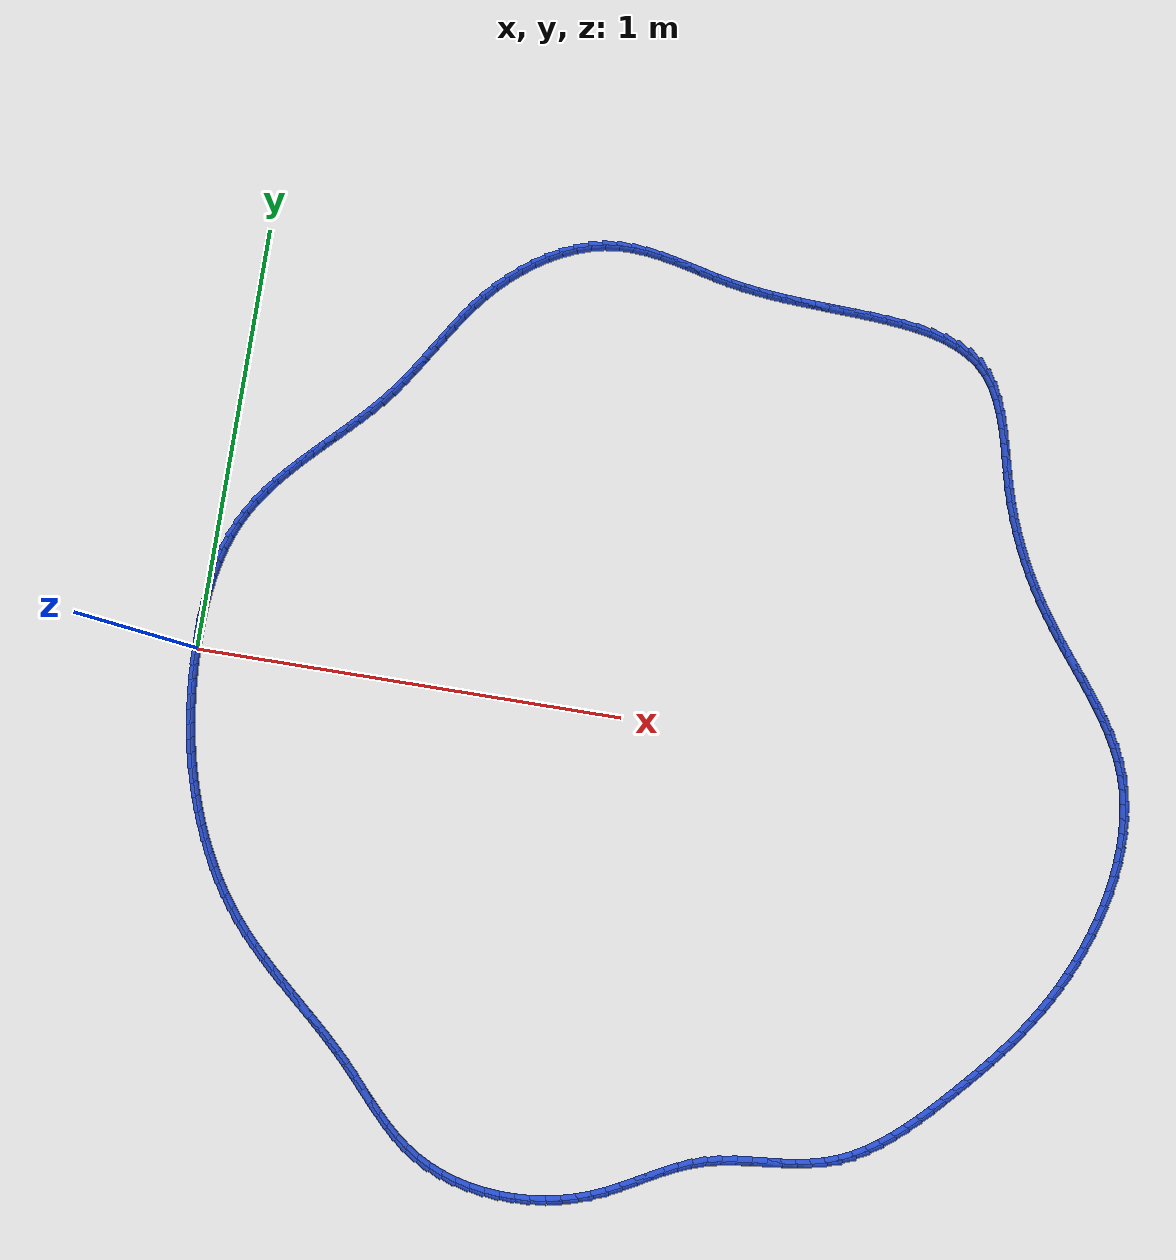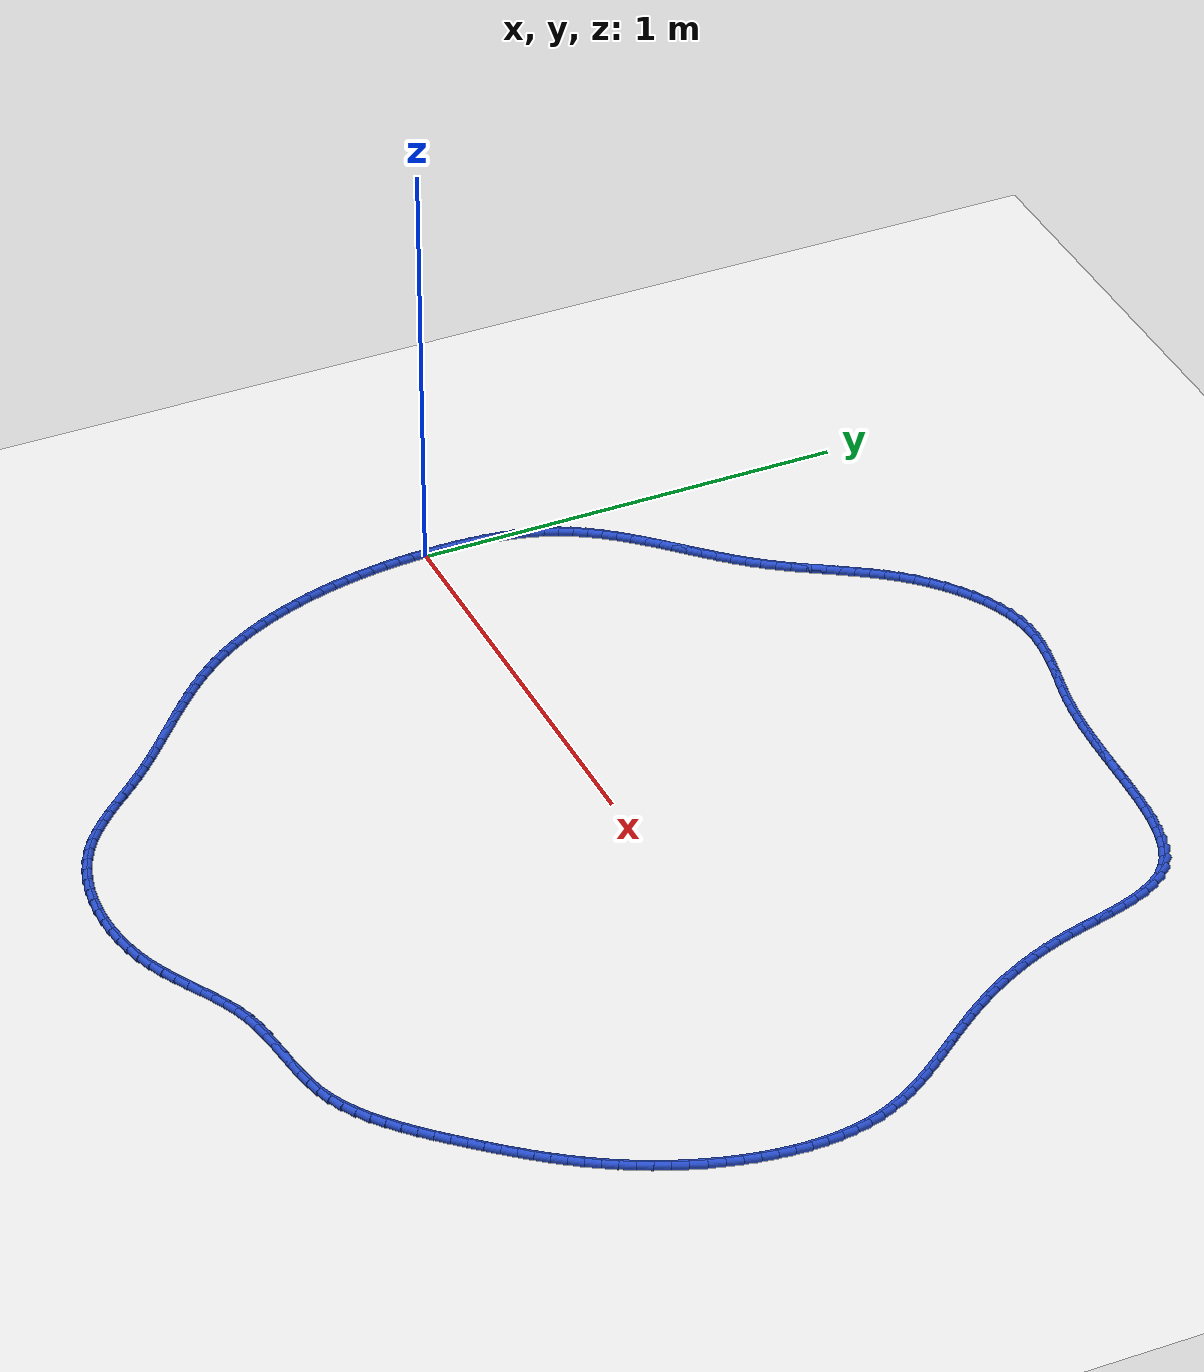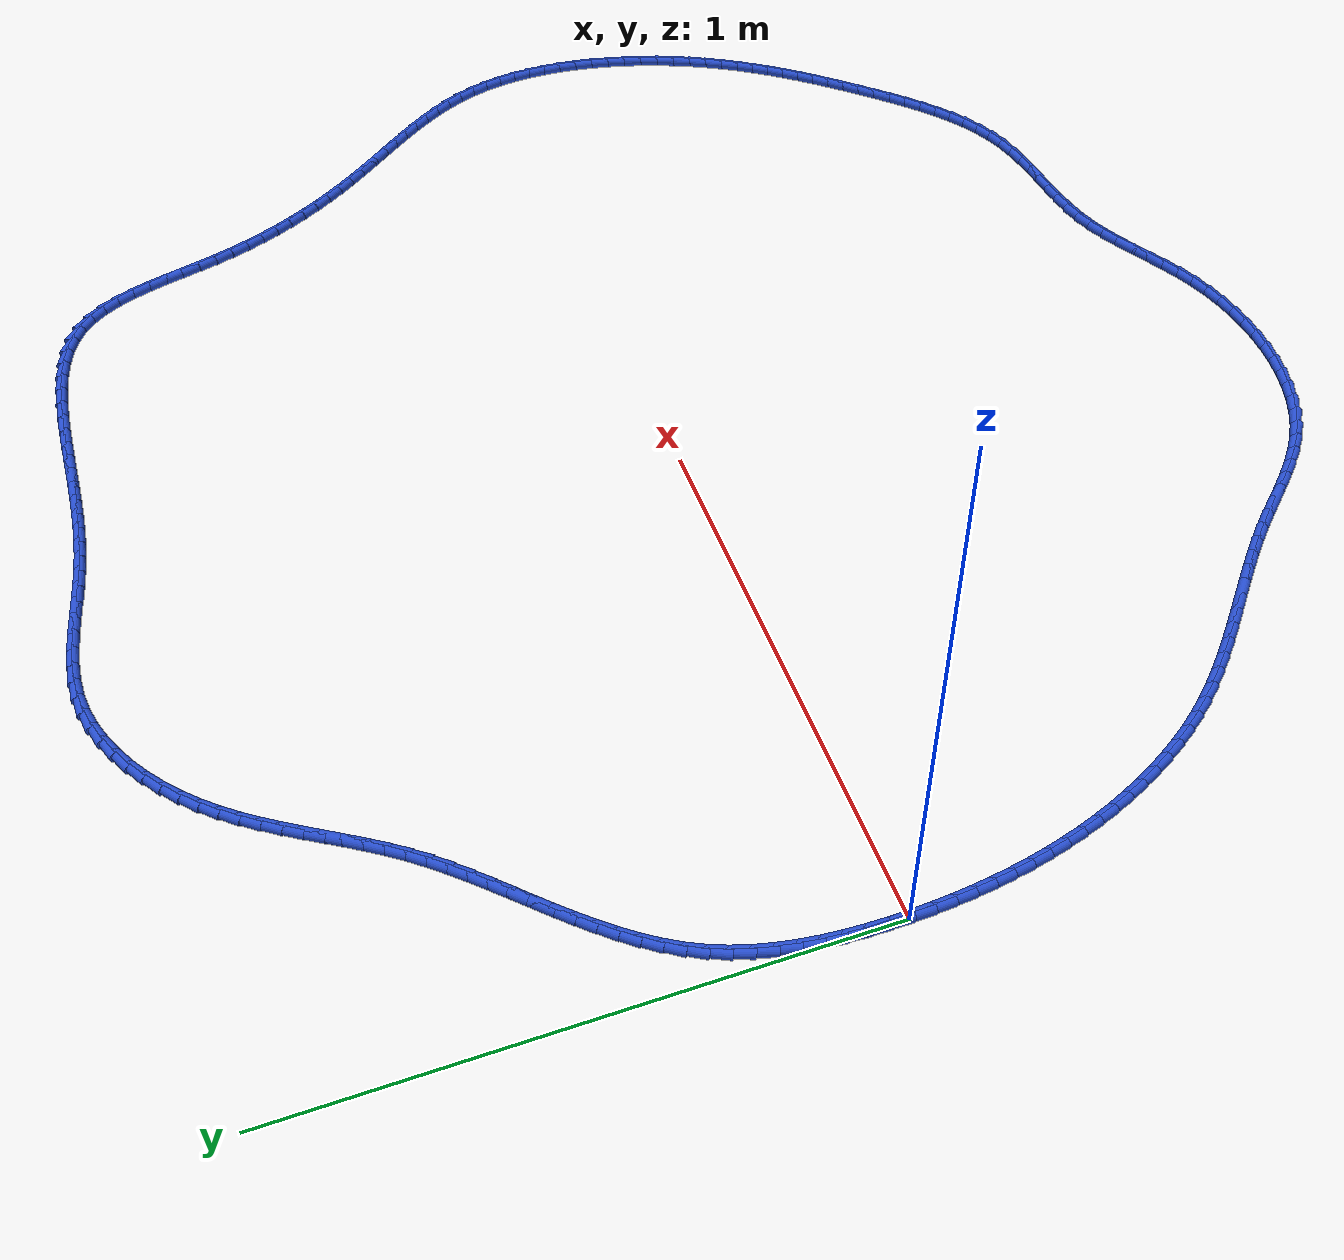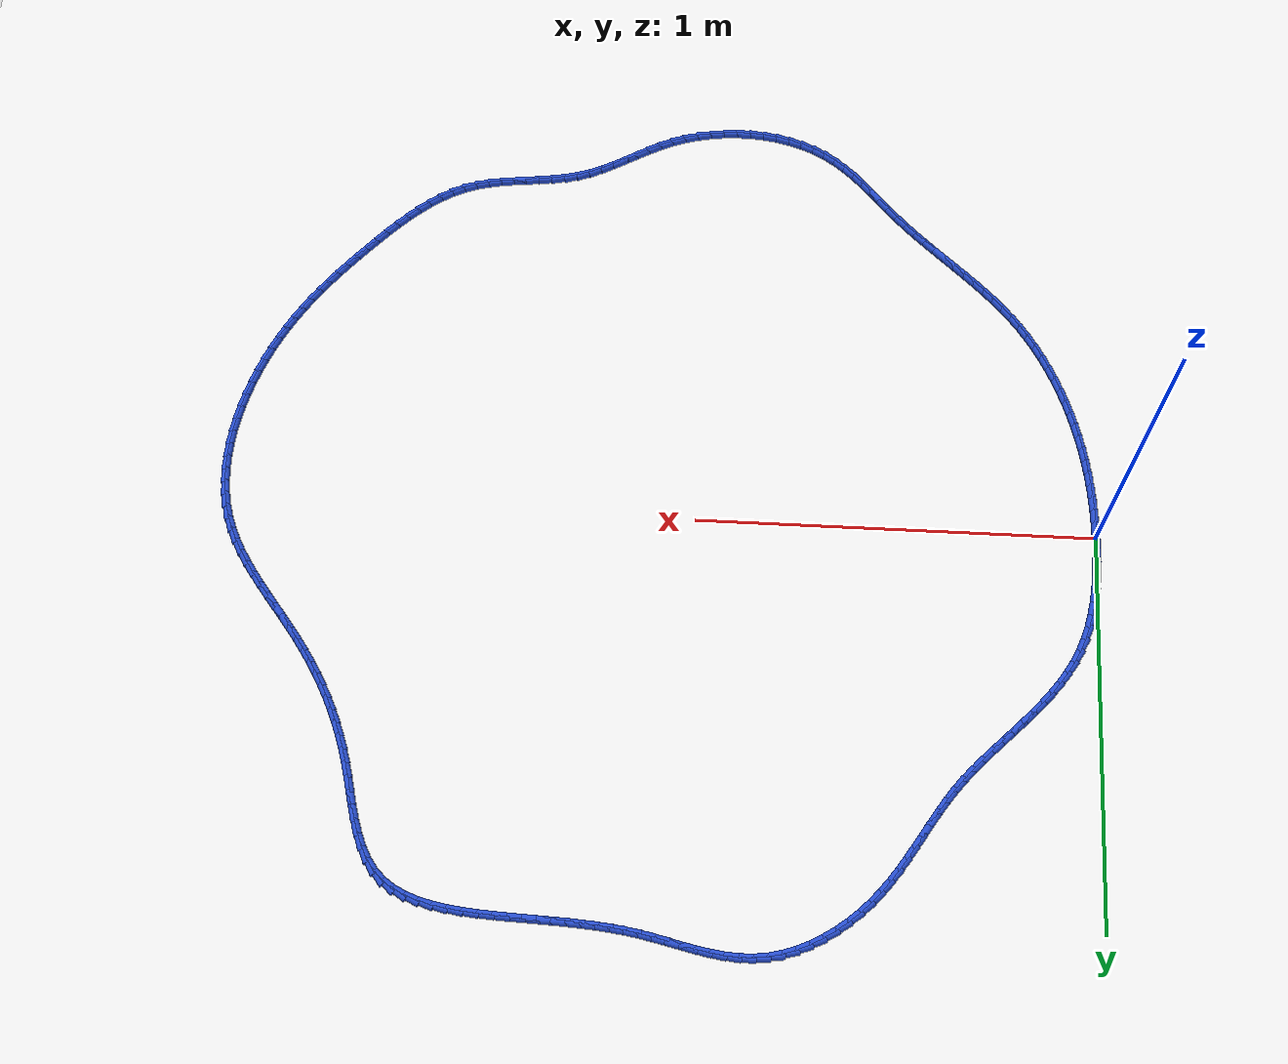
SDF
<sdf version="1.6">
 <world name="default">
  <light name="sun" type="directional">
   <pose>0 0 10 0 -0 0</pose>
   <diffuse>0.8 0.8 0.8 1</diffuse>
   <specular>0.2 0.2 0.2 1</specular>
   <attenuation>
    <range>1000</range>
    <constant>0.9</constant>
    <linear>0.01</linear>
    <quadratic>0.001</quadratic>
   </attenuation>
   <direction>-0.5 0.1 -0.9</direction>
  </light>
  <model name="ground_plane">
   <static>1</static>
   <link name="link">
    <collision name="collision">
     <geometry><plane><normal>0 0 1</normal><size>100 100</size></plane></geometry>
     <surface><friction><ode><mu>100</mu><mu2>50</mu2></ode></friction></surface>
    </collision>
    <visual name="visual">
     <cast_shadows>0</cast_shadows>
     <geometry><plane><normal>0 0 1</normal><size>100 100</size></plane></geometry>
     <material>
      <script><uri>file://media/materials/scripts/gazebo.material</uri><name>Gazebo/WhiteGlow</name></script>
     </material>
    </visual>
   </link>
  </model>
  <gravity>0 0 -9.8</gravity>
  <magnetic_field>6e-06 2.3e-05 -4.2e-05</magnetic_field>
  <atmosphere type="adiabatic"/>
  <physics name="default_physics" default="0" type="ode">
   <max_step_size>0.001</max_step_size>
   <real_time_factor>1</real_time_factor>
   <real_time_update_rate>1000</real_time_update_rate>
  </physics>
  <scene><ambient>0.4 0.4 0.4 1</ambient><background>0.7 0.7 0.7 1</background><shadows>1</shadows></scene>
  <spherical_coordinates>
   <surface_model>EARTH_WGS84</surface_model>
   <latitude_deg>0</latitude_deg>
   <longitude_deg>0</longitude_deg>
   <elevation>0</elevation>
   <heading_deg>0</heading_deg>
  </spherical_coordinates>
  <model name="line">
   <link name="link_0">
    <pose>4.336808689942018e-18 -4.85722573273506e-17 0.01 0 1.57 -1.5551713385921593</pose>
    <collision name="collision">
     <geometry><cylinder><radius>0.01</radius><length>0.08</length></cylinder></geometry>
    </collision>
    <visual name="visual">
     <material>
      <script><name>Gazebo/Blue</name><uri>file://media/materials/scripts/gazebo.material</uri></script>
     </material>
     <geometry><cylinder><radius>0.01</radius><length>0.08</length></cylinder></geometry>
    </visual>
   </link>
   <link name="link_1">
    <pose>-0.0005454513729576565 0.03490607328972473 0.01 0 1.57 1.5572508770001114</pose>
    <collision name="collision">
     <geometry><cylinder><radius>0.01</radius><length>0.08</length></cylinder></geometry>
    </collision>
    <visual name="visual">
     <material>
      <script><name>Gazebo/Blue</name><uri>file://media/materials/scripts/gazebo.material</uri></script>
     </material>
     <geometry><cylinder><radius>0.01</radius><length>0.08</length></cylinder></geometry>
    </visual>
   </link>
   <link name="link_2">
    <pose>-7.11422814879902e-05 0.0699200513916747 0.01 0 1.57 1.5231089749024698</pose>
    <collision name="collision">
     <geometry><cylinder><radius>0.01</radius><length>0.08</length></cylinder></geometry>
    </collision>
    <visual name="visual">
     <material>
      <script><name>Gazebo/Blue</name><uri>file://media/materials/scripts/gazebo.material</uri></script>
     </material>
     <geometry><cylinder><radius>0.01</radius><length>0.08</length></cylinder></geometry>
    </visual>
   </link>
   <link name="link_3">
    <pose>0.0015967305746672651 0.10486869719056198 0.01 0 1.57 1.483572701808403</pose>
    <collision name="collision">
     <geometry><cylinder><radius>0.01</radius><length>0.08</length></cylinder></geometry>
    </collision>
    <visual name="visual">
     <material>
      <script><name>Gazebo/Blue</name><uri>file://media/materials/scripts/gazebo.material</uri></script>
     </material>
     <geometry><cylinder><radius>0.01</radius><length>0.08</length></cylinder></geometry>
    </visual>
   </link>
   <link name="link_4">
    <pose>0.004631970495766368 0.13957877357109874 0.01 0 1.57 1.4381500426747797</pose>
    <collision name="collision">
     <geometry><cylinder><radius>0.01</radius><length>0.08</length></cylinder></geometry>
    </collision>
    <visual name="visual">
     <material>
      <script><name>Gazebo/Blue</name><uri>file://media/materials/scripts/gazebo.material</uri></script>
     </material>
     <geometry><cylinder><radius>0.01</radius><length>0.08</length></cylinder></geometry>
    </visual>
   </link>
   <link name="link_5">
    <pose>0.009208380782067583 0.1738770434179972 0.01 0 1.57 1.3863037366777013</pose>
    <collision name="collision">
     <geometry><cylinder><radius>0.01</radius><length>0.08</length></cylinder></geometry>
    </collision>
    <visual name="visual">
     <material>
      <script><name>Gazebo/Blue</name><uri>file://media/materials/scripts/gazebo.material</uri></script>
     </material>
     <geometry><cylinder><radius>0.01</radius><length>0.08</length></cylinder></geometry>
    </visual>
   </link>
   <link name="link_6">
    <pose>0.01549976473382917 0.2075902696159695 0.01 0 1.57 1.3274912468184805</pose>
    <collision name="collision">
     <geometry><cylinder><radius>0.01</radius><length>0.08</length></cylinder></geometry>
    </collision>
    <visual name="visual">
     <material>
      <script><name>Gazebo/Blue</name><uri>file://media/materials/scripts/gazebo.material</uri></script>
     </material>
     <geometry><cylinder><radius>0.01</radius><length>0.08</length></cylinder></geometry>
    </visual>
   </link>
   <link name="link_7">
    <pose>0.023679925651309403 0.2405452150497278 0.01 0 1.57 1.2612280985428281</pose>
    <collision name="collision">
     <geometry><cylinder><radius>0.01</radius><length>0.08</length></cylinder></geometry>
    </collision>
    <visual name="visual">
     <material>
      <script><name>Gazebo/Blue</name><uri>file://media/materials/scripts/gazebo.material</uri></script>
     </material>
     <geometry><cylinder><radius>0.01</radius><length>0.08</length></cylinder></geometry>
    </visual>
   </link>
   <link name="link_8">
    <pose>0.03392266683476651 0.27256864260398433 0.01 0 1.57 1.1871806663778266</pose>
    <collision name="collision">
     <geometry><cylinder><radius>0.01</radius><length>0.08</length></cylinder></geometry>
    </collision>
    <visual name="visual">
     <material>
      <script><name>Gazebo/Blue</name><uri>file://media/materials/scripts/gazebo.material</uri></script>
     </material>
     <geometry><cylinder><radius>0.01</radius><length>0.08</length></cylinder></geometry>
    </visual>
   </link>
   <link name="link_9">
    <pose>0.0464017915844588 0.30348731516345123 0.01 0 1.57 1.1068186664397115</pose>
    <collision name="collision">
     <geometry><cylinder><radius>0.01</radius><length>0.08</length></cylinder></geometry>
    </collision>
    <visual name="visual">
     <material>
      <script><name>Gazebo/Blue</name><uri>file://media/materials/scripts/gazebo.material</uri></script>
     </material>
     <geometry><cylinder><radius>0.01</radius><length>0.08</length></cylinder></geometry>
    </visual>
   </link>
   <link name="link_10">
    <pose>0.06124946907298046 0.33315818382276774 0.01 0 1.57 1.031359643664135</pose>
    <collision name="collision">
     <geometry><cylinder><radius>0.01</radius><length>0.08</length></cylinder></geometry>
    </collision>
    <visual name="visual">
     <material>
      <script><name>Gazebo/Blue</name><uri>file://media/materials/scripts/gazebo.material</uri></script>
     </material>
     <geometry><cylinder><radius>0.01</radius><length>0.08</length></cylinder></geometry>
    </visual>
   </link>
   <link name="link_11">
    <pose>0.07830627582986859 0.3616496286271902 0.01 0 1.57 0.9661470551166617</pose>
    <collision name="collision">
     <geometry><cylinder><radius>0.01</radius><length>0.08</length></cylinder></geometry>
    </collision>
    <visual name="visual">
     <material>
      <script><name>Gazebo/Blue</name><uri>file://media/materials/scripts/gazebo.material</uri></script>
     </material>
     <geometry><cylinder><radius>0.01</radius><length>0.08</length></cylinder></geometry>
    </visual>
   </link>
   <link name="link_12">
    <pose>0.09728814360428557 0.38912040746840487 0.01 0 1.57 0.9114803288456177</pose>
    <collision name="collision">
     <geometry><cylinder><radius>0.01</radius><length>0.08</length></cylinder></geometry>
    </collision>
    <visual name="visual">
     <material>
      <script><name>Gazebo/Blue</name><uri>file://media/materials/scripts/gazebo.material</uri></script>
     </material>
     <geometry><cylinder><radius>0.01</radius><length>0.08</length></cylinder></geometry>
    </visual>
   </link>
   <link name="link_13">
    <pose>0.11791053476553841 0.4157296185775842 0.01 0 1.57 0.867252139046164</pose>
    <collision name="collision">
     <geometry><cylinder><radius>0.01</radius><length>0.08</length></cylinder></geometry>
    </collision>
    <visual name="visual">
     <material>
      <script><name>Gazebo/Blue</name><uri>file://media/materials/scripts/gazebo.material</uri></script>
     </material>
     <geometry><cylinder><radius>0.01</radius><length>0.08</length></cylinder></geometry>
    </visual>
   </link>
   <link name="link_14">
    <pose>0.13988891168293402 0.44163636018590086 0.01 0 1.57 0.8331493308550025</pose>
    <collision name="collision">
     <geometry><cylinder><radius>0.01</radius><length>0.08</length></cylinder></geometry>
    </collision>
    <visual name="visual">
     <material>
      <script><name>Gazebo/Blue</name><uri>file://media/materials/scripts/gazebo.material</uri></script>
     </material>
     <geometry><cylinder><radius>0.01</radius><length>0.08</length></cylinder></geometry>
    </visual>
   </link>
   <link name="link_15">
    <pose>0.16293873672577916 0.466999730524527 0.01 0 1.57 0.8087953530941996</pose>
    <collision name="collision">
     <geometry><cylinder><radius>0.01</radius><length>0.08</length></cylinder></geometry>
    </collision>
    <visual name="visual">
     <material>
      <script><name>Gazebo/Blue</name><uri>file://media/materials/scripts/gazebo.material</uri></script>
     </material>
     <geometry><cylinder><radius>0.01</radius><length>0.08</length></cylinder></geometry>
    </visual>
   </link>
   <link name="link_16">
    <pose>0.18677547226338106 0.4919788278246356 0.01 0 1.57 0.7938475137856855</pose>
    <collision name="collision">
     <geometry><cylinder><radius>0.01</radius><length>0.08</length></cylinder></geometry>
    </collision>
    <visual name="visual">
     <material>
      <script><name>Gazebo/Blue</name><uri>file://media/materials/scripts/gazebo.material</uri></script>
     </material>
     <geometry><cylinder><radius>0.01</radius><length>0.08</length></cylinder></geometry>
    </visual>
   </link>
   <link name="link_17">
    <pose>0.21111458066504654 0.5167327503173987 0.01 0 1.57 0.7880563527090264</pose>
    <collision name="collision">
     <geometry><cylinder><radius>0.01</radius><length>0.08</length></cylinder></geometry>
    </collision>
    <visual name="visual">
     <material>
      <script><name>Gazebo/Blue</name><uri>file://media/materials/scripts/gazebo.material</uri></script>
     </material>
     <geometry><cylinder><radius>0.01</radius><length>0.08</length></cylinder></geometry>
    </visual>
   </link>
   <link name="link_18">
    <pose>0.23567152430008248 0.5414205962339891 0.01 0 1.57 0.7912966091688998</pose>
    <collision name="collision">
     <geometry><cylinder><radius>0.01</radius><length>0.08</length></cylinder></geometry>
    </collision>
    <visual name="visual">
     <material>
      <script><name>Gazebo/Blue</name><uri>file://media/materials/scripts/gazebo.material</uri></script>
     </material>
     <geometry><cylinder><radius>0.01</radius><length>0.08</length></cylinder></geometry>
    </visual>
   </link>
   <link name="link_19">
    <pose>0.26016176553779596 0.5662014638055791 0.01 0 1.57 0.8035769638067028</pose>
    <collision name="collision">
     <geometry><cylinder><radius>0.01</radius><length>0.08</length></cylinder></geometry>
    </collision>
    <visual name="visual">
     <material>
      <script><name>Gazebo/Blue</name><uri>file://media/materials/scripts/gazebo.material</uri></script>
     </material>
     <geometry><cylinder><radius>0.01</radius><length>0.08</length></cylinder></geometry>
    </visual>
   </link>
   <link name="link_20">
    <pose>0.2843007667474938 0.5912344512633414 0.01 0 1.57 0.8250318200943751</pose>
    <collision name="collision">
     <geometry><cylinder><radius>0.01</radius><length>0.08</length></cylinder></geometry>
    </collision>
    <visual name="visual">
     <material>
      <script><name>Gazebo/Blue</name><uri>file://media/materials/scripts/gazebo.material</uri></script>
     </material>
     <geometry><cylinder><radius>0.01</radius><length>0.08</length></cylinder></geometry>
    </visual>
   </link>
   <link name="link_21">
    <pose>0.30780399029848293 0.6166786568384481 0.01 0 1.57 0.8558942179228385</pose>
    <collision name="collision">
     <geometry><cylinder><radius>0.01</radius><length>0.08</length></cylinder></geometry>
    </collision>
    <visual name="visual">
     <material>
      <script><name>Gazebo/Blue</name><uri>file://media/materials/scripts/gazebo.material</uri></script>
     </material>
     <geometry><cylinder><radius>0.01</radius><length>0.08</length></cylinder></geometry>
    </visual>
   </link>
   <link name="link_22">
    <pose>0.33038689856007036 0.6426931787620722 0.01 0 1.57 0.8964234375971111</pose>
    <collision name="collision">
     <geometry><cylinder><radius>0.01</radius><length>0.08</length></cylinder></geometry>
    </collision>
    <visual name="visual">
     <material>
      <script><name>Gazebo/Blue</name><uri>file://media/materials/scripts/gazebo.material</uri></script>
     </material>
     <geometry><cylinder><radius>0.01</radius><length>0.08</length></cylinder></geometry>
    </visual>
   </link>
   <link name="link_23">
    <pose>0.3517656094628502 0.669436739701347 0.01 0 1.57 0.9411124589400269</pose>
    <collision name="collision">
     <geometry><cylinder><radius>0.01</radius><length>0.08</length></cylinder></geometry>
    </collision>
    <visual name="visual">
     <material>
      <script><name>Gazebo/Blue</name><uri>file://media/materials/scripts/gazebo.material</uri></script>
     </material>
     <geometry><cylinder><radius>0.01</radius><length>0.08</length></cylinder></geometry>
    </visual>
   </link>
   <link name="link_24">
    <pose>0.37182725326284466 0.6969700911940012 0.01 0 1.57 0.97642816466721</pose>
    <collision name="collision">
     <geometry><cylinder><radius>0.01</radius><length>0.08</length></cylinder></geometry>
    </collision>
    <visual name="visual">
     <material>
      <script><name>Gazebo/Blue</name><uri>file://media/materials/scripts/gazebo.material</uri></script>
     </material>
     <geometry><cylinder><radius>0.01</radius><length>0.08</length></cylinder></geometry>
    </visual>
   </link>
   <link name="link_25">
    <pose>0.39085759008717813 0.7251256139946143 0.01 0 1.57 1.000197946043899</pose>
    <collision name="collision">
     <geometry><cylinder><radius>0.01</radius><length>0.08</length></cylinder></geometry>
    </collision>
    <visual name="visual">
     <material>
      <script><name>Gazebo/Blue</name><uri>file://media/materials/scripts/gazebo.material</uri></script>
     </material>
     <geometry><cylinder><radius>0.01</radius><length>0.08</length></cylinder></geometry>
    </visual>
   </link>
   <link name="link_26">
    <pose>0.40919906751452423 0.7537032132239931 0.01 0 1.57 1.0123136852721775</pose>
    <collision name="collision">
     <geometry><cylinder><radius>0.01</radius><length>0.08</length></cylinder></geometry>
    </collision>
    <visual name="visual">
     <material>
      <script><name>Gazebo/Blue</name><uri>file://media/materials/scripts/gazebo.material</uri></script>
     </material>
     <geometry><cylinder><radius>0.01</radius><length>0.08</length></cylinder></geometry>
    </visual>
   </link>
   <link name="link_27">
    <pose>0.4271941331235565 0.7825027940029446 0.01 0 1.57 1.0127539883543581</pose>
    <collision name="collision">
     <geometry><cylinder><radius>0.01</radius><length>0.08</length></cylinder></geometry>
    </collision>
    <visual name="visual">
     <material>
      <script><name>Gazebo/Blue</name><uri>file://media/materials/scripts/gazebo.material</uri></script>
     </material>
     <geometry><cylinder><radius>0.01</radius><length>0.08</length></cylinder></geometry>
    </visual>
   </link>
   <link name="link_28">
    <pose>0.44518523449294795 0.8113242614522748 0.01 0 1.57 1.0015351789754492</pose>
    <collision name="collision">
     <geometry><cylinder><radius>0.01</radius><length>0.08</length></cylinder></geometry>
    </collision>
    <visual name="visual">
     <material>
      <script><name>Gazebo/Blue</name><uri>file://media/materials/scripts/gazebo.material</uri></script>
     </material>
     <geometry><cylinder><radius>0.01</radius><length>0.08</length></cylinder></geometry>
    </visual>
   </link>
   <link name="link_29">
    <pose>0.4635148192013722 0.8399675206927902 0.01 0 1.57 0.9787093027036249</pose>
    <collision name="collision">
     <geometry><cylinder><radius>0.01</radius><length>0.08</length></cylinder></geometry>
    </collision>
    <visual name="visual">
     <material>
      <script><name>Gazebo/Blue</name><uri>file://media/materials/scripts/gazebo.material</uri></script>
     </material>
     <geometry><cylinder><radius>0.01</radius><length>0.08</length></cylinder></geometry>
    </visual>
   </link>
   <link name="link_30">
    <pose>0.482525334827503 0.8682324768452984 0.01 0 1.57 0.944408757813209</pose>
    <collision name="collision">
     <geometry><cylinder><radius>0.01</radius><length>0.08</length></cylinder></geometry>
    </collision>
    <visual name="visual">
     <material>
      <script><name>Gazebo/Blue</name><uri>file://media/materials/scripts/gazebo.material</uri></script>
     </material>
     <geometry><cylinder><radius>0.01</radius><length>0.08</length></cylinder></geometry>
    </visual>
   </link>
   <link name="link_31">
    <pose>0.5025592289500133 0.895919035030605 0.01 0 1.57 0.8989338296471515</pose>
    <collision name="collision">
     <geometry><cylinder><radius>0.01</radius><length>0.08</length></cylinder></geometry>
    </collision>
    <visual name="visual">
     <material>
      <script><name>Gazebo/Blue</name><uri>file://media/materials/scripts/gazebo.material</uri></script>
     </material>
     <geometry><cylinder><radius>0.01</radius><length>0.08</length></cylinder></geometry>
    </visual>
   </link>
   <link name="link_32">
    <pose>0.5239589491475768 0.9228271003695171 0.01 0 1.57 0.8429076313974756</pose>
    <collision name="collision">
     <geometry><cylinder><radius>0.01</radius><length>0.08</length></cylinder></geometry>
    </collision>
    <visual name="visual">
     <material>
      <script><name>Gazebo/Blue</name><uri>file://media/materials/scripts/gazebo.material</uri></script>
     </material>
     <geometry><cylinder><radius>0.01</radius><length>0.08</length></cylinder></geometry>
    </visual>
   </link>
   <link name="link_33">
    <pose>0.5470649551654392 0.9487562023604562 0.01 0 1.57 0.7802118866494246</pose>
    <collision name="collision">
     <geometry><cylinder><radius>0.01</radius><length>0.08</length></cylinder></geometry>
    </collision>
    <visual name="visual">
     <material>
      <script><name>Gazebo/Blue</name><uri>file://media/materials/scripts/gazebo.material</uri></script>
     </material>
     <geometry><cylinder><radius>0.01</radius><length>0.08</length></cylinder></geometry>
    </visual>
   </link>
   <link name="link_34">
    <pose>0.5720384568948993 0.9734719993249351 0.01 0 1.57 0.715855679188438</pose>
    <collision name="collision">
     <geometry><cylinder><radius>0.01</radius><length>0.08</length></cylinder></geometry>
    </collision>
    <visual name="visual">
     <material>
      <script><name>Gazebo/Blue</name><uri>file://media/materials/scripts/gazebo.material</uri></script>
     </material>
     <geometry><cylinder><radius>0.01</radius><length>0.08</length></cylinder></geometry>
    </visual>
   </link>
   <link name="link_35">
    <pose>0.5987214142825881 0.9966798238931742 0.01 0 1.57 0.6491029901672987</pose>
    <collision name="collision">
     <geometry><cylinder><radius>0.01</radius><length>0.08</length></cylinder></geometry>
    </collision>
    <visual name="visual">
     <material>
      <script><name>Gazebo/Blue</name><uri>file://media/materials/scripts/gazebo.material</uri></script>
     </material>
     <geometry><cylinder><radius>0.01</radius><length>0.08</length></cylinder></geometry>
    </visual>
   </link>
   <link name="link_36">
    <pose>0.6269228405587489 1.018078783060979 0.01 0 1.57 0.5786432785679712</pose>
    <collision name="collision">
     <geometry><cylinder><radius>0.01</radius><length>0.08</length></cylinder></geometry>
    </collision>
    <visual name="visual">
     <material>
      <script><name>Gazebo/Blue</name><uri>file://media/materials/scripts/gazebo.material</uri></script>
     </material>
     <geometry><cylinder><radius>0.01</radius><length>0.08</length></cylinder></geometry>
    </visual>
   </link>
   <link name="link_37">
    <pose>0.656451748953627 1.0373679838241572 0.01 0 1.57 0.5031580478176646</pose>
    <collision name="collision">
     <geometry><cylinder><radius>0.01</radius><length>0.08</length></cylinder></geometry>
    </collision>
    <visual name="visual">
     <material>
      <script><name>Gazebo/Blue</name><uri>file://media/materials/scripts/gazebo.material</uri></script>
     </material>
     <geometry><cylinder><radius>0.01</radius><length>0.08</length></cylinder></geometry>
    </visual>
   </link>
   <link name="link_38">
    <pose>0.6871171526974661 1.0542465331785142 0.01 0 1.57 0.4213295366004876</pose>
    <collision name="collision">
     <geometry><cylinder><radius>0.01</radius><length>0.08</length></cylinder></geometry>
    </collision>
    <visual name="visual">
     <material>
      <script><name>Gazebo/Blue</name><uri>file://media/materials/scripts/gazebo.material</uri></script>
     </material>
     <geometry><cylinder><radius>0.01</radius><length>0.08</length></cylinder></geometry>
    </visual>
   </link>
   <link name="link_39">
    <pose>0.7187280650205103 1.0684135381198572 0.01 0 1.57 0.33189579166244354</pose>
    <collision name="collision">
     <geometry><cylinder><radius>0.01</radius><length>0.08</length></cylinder></geometry>
    </collision>
    <visual name="visual">
     <material>
      <script><name>Gazebo/Blue</name><uri>file://media/materials/scripts/gazebo.material</uri></script>
     </material>
     <geometry><cylinder><radius>0.01</radius><length>0.08</length></cylinder></geometry>
    </visual>
   </link>
   <link name="link_40">
    <pose>0.751093499153004 1.0795681056439916 0.01 0 1.57 0.2337721022812503</pose>
    <collision name="collision">
     <geometry><cylinder><radius>0.01</radius><length>0.08</length></cylinder></geometry>
    </collision>
    <visual name="visual">
     <material>
      <script><name>Gazebo/Blue</name><uri>file://media/materials/scripts/gazebo.material</uri></script>
     </material>
     <geometry><cylinder><radius>0.01</radius><length>0.08</length></cylinder></geometry>
    </visual>
   </link>
   <link name="link_41">
    <pose>0.7840224683251918 1.0874093427467255 0.01 0 1.57 0.12646672706477355</pose>
    <collision name="collision">
     <geometry><cylinder><radius>0.01</radius><length>0.08</length></cylinder></geometry>
    </collision>
    <visual name="visual">
     <material>
      <script><name>Gazebo/Blue</name><uri>file://media/materials/scripts/gazebo.material</uri></script>
     </material>
     <geometry><cylinder><radius>0.01</radius><length>0.08</length></cylinder></geometry>
    </visual>
   </link>
   <link name="link_42">
    <pose>0.8173250234270161 1.0916436060331283 0.01 0 1.57 0.020659050336729705</pose>
    <collision name="collision">
     <geometry><cylinder><radius>0.01</radius><length>0.08</length></cylinder></geometry>
    </collision>
    <visual name="visual">
     <material>
      <script><name>Gazebo/Blue</name><uri>file://media/materials/scripts/gazebo.material</uri></script>
     </material>
     <geometry><cylinder><radius>0.01</radius><length>0.08</length></cylinder></geometry>
    </visual>
   </link>
   <link name="link_43">
    <pose>0.8508626442353454 1.0923365600157995 0.01 0 1.57 -0.06710515468268982</pose>
    <collision name="collision">
     <geometry><cylinder><radius>0.01</radius><length>0.08</length></cylinder></geometry>
    </collision>
    <visual name="visual">
     <material>
      <script><name>Gazebo/Blue</name><uri>file://media/materials/scripts/gazebo.material</uri></script>
     </material>
     <geometry><cylinder><radius>0.01</radius><length>0.08</length></cylinder></geometry>
    </visual>
   </link>
   <link name="link_44">
    <pose>0.8845708525840756 1.0900711640229632 0.01 0 1.57 -0.13520231619304565</pose>
    <collision name="collision">
     <geometry><cylinder><radius>0.01</radius><length>0.08</length></cylinder></geometry>
    </collision>
    <visual name="visual">
     <material>
      <script><name>Gazebo/Blue</name><uri>file://media/materials/scripts/gazebo.material</uri></script>
     </material>
     <geometry><cylinder><radius>0.01</radius><length>0.08</length></cylinder></geometry>
    </visual>
   </link>
   <link name="link_45">
    <pose>0.9183909197407225 1.0854705457996023 0.01 0 1.57 -0.1842493978542337</pose>
    <collision name="collision">
     <geometry><cylinder><radius>0.01</radius><length>0.08</length></cylinder></geometry>
    </collision>
    <visual name="visual">
     <material>
      <script><name>Gazebo/Blue</name><uri>file://media/materials/scripts/gazebo.material</uri></script>
     </material>
     <geometry><cylinder><radius>0.01</radius><length>0.08</length></cylinder></geometry>
    </visual>
   </link>
   <link name="link_46">
    <pose>0.952264116972802 1.0791578330906992 0.01 0 1.57 -0.21516445164552903</pose>
    <collision name="collision">
     <geometry><cylinder><radius>0.01</radius><length>0.08</length></cylinder></geometry>
    </collision>
    <visual name="visual">
     <material>
      <script><name>Gazebo/Blue</name><uri>file://media/materials/scripts/gazebo.material</uri></script>
     </material>
     <geometry><cylinder><radius>0.01</radius><length>0.08</length></cylinder></geometry>
    </visual>
   </link>
   <link name="link_47">
    <pose>0.9861317155478289 1.071756153641235 0.01 0 1.57 -0.22867323404507947</pose>
    <collision name="collision">
     <geometry><cylinder><radius>0.01</radius><length>0.08</length></cylinder></geometry>
    </collision>
    <visual name="visual">
     <material>
      <script><name>Gazebo/Blue</name><uri>file://media/materials/scripts/gazebo.material</uri></script>
     </material>
     <geometry><cylinder><radius>0.01</radius><length>0.08</length></cylinder></geometry>
    </visual>
   </link>
   <link name="link_48">
    <pose>1.0199349867333196 1.0638886351961927 0.01 0 1.57 -0.225046776954098</pose>
    <collision name="collision">
     <geometry><cylinder><radius>0.01</radius><length>0.08</length></cylinder></geometry>
    </collision>
    <visual name="visual">
     <material>
      <script><name>Gazebo/Blue</name><uri>file://media/materials/scripts/gazebo.material</uri></script>
     </material>
     <geometry><cylinder><radius>0.01</radius><length>0.08</length></cylinder></geometry>
    </visual>
   </link>
   <link name="link_49">
    <pose>1.0536152017967901 1.056178405500555 0.01 0 1.57 -0.2039931108099421</pose>
    <collision name="collision">
     <geometry><cylinder><radius>0.01</radius><length>0.08</length></cylinder></geometry>
    </collision>
    <visual name="visual">
     <material>
      <script><name>Gazebo/Blue</name><uri>file://media/materials/scripts/gazebo.material</uri></script>
     </material>
     <geometry><cylinder><radius>0.01</radius><length>0.08</length></cylinder></geometry>
    </visual>
   </link>
   <link name="link_50">
    <pose>1.0871136379834587 1.0492485632865867 0.01 0 1.57 -0.16918378252128569</pose>
    <collision name="collision">
     <geometry><cylinder><radius>0.01</radius><length>0.08</length></cylinder></geometry>
    </collision>
    <visual name="visual">
     <material>
      <script><name>Gazebo/Blue</name><uri>file://media/materials/scripts/gazebo.material</uri></script>
     </material>
     <geometry><cylinder><radius>0.01</radius><length>0.08</length></cylinder></geometry>
    </visual>
   </link>
   <link name="link_51">
    <pose>1.1204045993406824 1.0435619120764832 0.01 0 1.57 -0.13534197490541341</pose>
    <collision name="collision">
     <geometry><cylinder><radius>0.01</radius><length>0.08</length></cylinder></geometry>
    </collision>
    <visual name="visual">
     <material>
      <script><name>Gazebo/Blue</name><uri>file://media/materials/scripts/gazebo.material</uri></script>
     </material>
     <geometry><cylinder><radius>0.01</radius><length>0.08</length></cylinder></geometry>
    </visual>
   </link>
   <link name="link_52">
    <pose>1.1535728276952377 1.0390452468809621 0.01 0 1.57 -0.10612881740557806</pose>
    <collision name="collision">
     <geometry><cylinder><radius>0.01</radius><length>0.08</length></cylinder></geometry>
    </collision>
    <visual name="visual">
     <material>
      <script><name>Gazebo/Blue</name><uri>file://media/materials/scripts/gazebo.material</uri></script>
     </material>
     <geometry><cylinder><radius>0.01</radius><length>0.08</length></cylinder></geometry>
    </visual>
   </link>
   <link name="link_53">
    <pose>1.186726121602748 1.0355134571384534 0.01 0 1.57 -0.08199142908092878</pose>
    <collision name="collision">
     <geometry><cylinder><radius>0.01</radius><length>0.08</length></cylinder></geometry>
    </collision>
    <visual name="visual">
     <material>
      <script><name>Gazebo/Blue</name><uri>file://media/materials/scripts/gazebo.material</uri></script>
     </material>
     <geometry><cylinder><radius>0.01</radius><length>0.08</length></cylinder></geometry>
    </visual>
   </link>
   <link name="link_54">
    <pose>1.2199722796188368 1.0327814322873867 0.01 0 1.57 -0.06322121916378484</pose>
    <collision name="collision">
     <geometry><cylinder><radius>0.01</radius><length>0.08</length></cylinder></geometry>
    </collision>
    <visual name="visual">
     <material>
      <script><name>Gazebo/Blue</name><uri>file://media/materials/scripts/gazebo.material</uri></script>
     </material>
     <geometry><cylinder><radius>0.01</radius><length>0.08</length></cylinder></geometry>
    </visual>
   </link>
   <link name="link_55">
    <pose>1.2534191002991268 1.0306640617661924 0.01 0 1.57 -0.049960247332221645</pose>
    <collision name="collision">
     <geometry><cylinder><radius>0.01</radius><length>0.08</length></cylinder></geometry>
    </collision>
    <visual name="visual">
     <material>
      <script><name>Gazebo/Blue</name><uri>file://media/materials/scripts/gazebo.material</uri></script>
     </material>
     <geometry><cylinder><radius>0.01</radius><length>0.08</length></cylinder></geometry>
    </visual>
   </link>
   <link name="link_56">
    <pose>1.2871743821992425 1.0289762350132998 0.01 0 1.57 -0.04221454360005864</pose>
    <collision name="collision">
     <geometry><cylinder><radius>0.01</radius><length>0.08</length></cylinder></geometry>
    </collision>
    <visual name="visual">
     <material>
      <script><name>Gazebo/Blue</name><uri>file://media/materials/scripts/gazebo.material</uri></script>
     </material>
     <geometry><cylinder><radius>0.01</radius><length>0.08</length></cylinder></geometry>
    </visual>
   </link>
   <link name="link_57">
    <pose>1.321345923874806 1.0275328414671394 0.01 0 1.57 -0.03987068725952909</pose>
    <collision name="collision">
     <geometry><cylinder><radius>0.01</radius><length>0.08</length></cylinder></geometry>
    </collision>
    <visual name="visual">
     <material>
      <script><name>Gazebo/Blue</name><uri>file://media/materials/scripts/gazebo.material</uri></script>
     </material>
     <geometry><cylinder><radius>0.01</radius><length>0.08</length></cylinder></geometry>
    </visual>
   </link>
   <link name="link_58">
    <pose>1.356041523881441 1.0261487705661412 0.01 0 1.57 -0.04271296731066947</pose>
    <collision name="collision">
     <geometry><cylinder><radius>0.01</radius><length>0.08</length></cylinder></geometry>
    </collision>
    <visual name="visual">
     <material>
      <script><name>Gazebo/Blue</name><uri>file://media/materials/scripts/gazebo.material</uri></script>
     </material>
     <geometry><cylinder><radius>0.01</radius><length>0.08</length></cylinder></geometry>
    </visual>
   </link>
   <link name="link_59">
    <pose>1.3913689807747713 1.0246389117487353 0.01 0 1.57 -0.0504639386554917</pose>
    <collision name="collision">
     <geometry><cylinder><radius>0.01</radius><length>0.08</length></cylinder></geometry>
    </collision>
    <visual name="visual">
     <material>
      <script><name>Gazebo/Blue</name><uri>file://media/materials/scripts/gazebo.material</uri></script>
     </material>
     <geometry><cylinder><radius>0.01</radius><length>0.08</length></cylinder></geometry>
    </visual>
   </link>
   <link name="link_60">
    <pose>1.427433895713201 1.0228173875944273 0.01 0 1.57 -0.06518867235303466</pose>
    <collision name="collision">
     <geometry><cylinder><radius>0.01</radius><length>0.08</length></cylinder></geometry>
    </collision>
    <visual name="visual">
     <material>
      <script><name>Gazebo/Blue</name><uri>file://media/materials/scripts/gazebo.material</uri></script>
     </material>
     <geometry><cylinder><radius>0.01</radius><length>0.08</length></cylinder></geometry>
    </visual>
   </link>
   <link name="link_61">
    <pose>1.4641238244778052 1.0204222260913827 0.01 0 1.57 -0.0913240121081484</pose>
    <collision name="collision">
     <geometry><cylinder><radius>0.01</radius><length>0.08</length></cylinder></geometry>
    </collision>
    <visual name="visual">
     <material>
      <script><name>Gazebo/Blue</name><uri>file://media/materials/scripts/gazebo.material</uri></script>
     </material>
     <geometry><cylinder><radius>0.01</radius><length>0.08</length></cylinder></geometry>
    </visual>
   </link>
   <link name="link_62">
    <pose>1.500926409776979 1.0170518915176316 0.01 0 1.57 -0.13022632659403668</pose>
    <collision name="collision">
     <geometry><cylinder><radius>0.01</radius><length>0.08</length></cylinder></geometry>
    </collision>
    <visual name="visual">
     <material>
      <script><name>Gazebo/Blue</name><uri>file://media/materials/scripts/gazebo.material</uri></script>
     </material>
     <geometry><cylinder><radius>0.01</radius><length>0.08</length></cylinder></geometry>
    </visual>
   </link>
   <link name="link_63">
    <pose>1.5372864731412006 1.0122899041974547 0.01 0 1.57 -0.18369951504137735</pose>
    <collision name="collision">
     <geometry><cylinder><radius>0.01</radius><length>0.08</length></cylinder></geometry>
    </collision>
    <visual name="visual">
     <material>
      <script><name>Gazebo/Blue</name><uri>file://media/materials/scripts/gazebo.material</uri></script>
     </material>
     <geometry><cylinder><radius>0.01</radius><length>0.08</length></cylinder></geometry>
    </visual>
   </link>
   <link name="link_64">
    <pose>1.5726488361009476 1.0057197844551313 0.01 0 1.57 -0.2544862424062755</pose>
    <collision name="collision">
     <geometry><cylinder><radius>0.01</radius><length>0.08</length></cylinder></geometry>
    </collision>
    <visual name="visual">
     <material>
      <script><name>Gazebo/Blue</name><uri>file://media/materials/scripts/gazebo.material</uri></script>
     </material>
     <geometry><cylinder><radius>0.01</radius><length>0.08</length></cylinder></geometry>
    </visual>
   </link>
   <link name="link_65">
    <pose>1.6064583201866989 0.9969250526149419 0.01 0 1.57 -0.34620636434738233</pose>
    <collision name="collision">
     <geometry><cylinder><radius>0.01</radius><length>0.08</length></cylinder></geometry>
    </collision>
    <visual name="visual">
     <material>
      <script><name>Gazebo/Blue</name><uri>file://media/materials/scripts/gazebo.material</uri></script>
     </material>
     <geometry><cylinder><radius>0.01</radius><length>0.08</length></cylinder></geometry>
    </visual>
   </link>
   <link name="link_66">
    <pose>1.6381597469289322 0.985489229001167 0.01 0 1.57 -0.4629393142172763</pose>
    <collision name="collision">
     <geometry><cylinder><radius>0.01</radius><length>0.08</length></cylinder></geometry>
    </collision>
    <visual name="visual">
     <material>
      <script><name>Gazebo/Blue</name><uri>file://media/materials/scripts/gazebo.material</uri></script>
     </material>
     <geometry><cylinder><radius>0.01</radius><length>0.08</length></cylinder></geometry>
    </visual>
   </link>
   <link name="link_67">
    <pose>1.6671979378581256 0.9709958339380858 0.01 0 1.57 -0.6079549868972415</pose>
    <collision name="collision">
     <geometry><cylinder><radius>0.01</radius><length>0.08</length></cylinder></geometry>
    </collision>
    <visual name="visual">
     <material>
      <script><name>Gazebo/Blue</name><uri>file://media/materials/scripts/gazebo.material</uri></script>
     </material>
     <geometry><cylinder><radius>0.01</radius><length>0.08</length></cylinder></geometry>
    </visual>
   </link>
   <link name="link_68">
    <pose>1.693017714504758 0.9530283877499792 0.01 0 1.57 -0.779305313178607</pose>
    <collision name="collision">
     <geometry><cylinder><radius>0.01</radius><length>0.08</length></cylinder></geometry>
    </collision>
    <visual name="visual">
     <material>
      <script><name>Gazebo/Blue</name><uri>file://media/materials/scripts/gazebo.material</uri></script>
     </material>
     <geometry><cylinder><radius>0.01</radius><length>0.08</length></cylinder></geometry>
    </visual>
   </link>
   <link name="link_69">
    <pose>1.7151061495331201 0.9312074890259554 0.01 0 1.57 -0.9443591813821003</pose>
    <collision name="collision">
     <geometry><cylinder><radius>0.01</radius><length>0.08</length></cylinder></geometry>
    </collision>
    <visual name="visual">
     <material>
      <script><name>Gazebo/Blue</name><uri>file://media/materials/scripts/gazebo.material</uri></script>
     </material>
     <geometry><cylinder><radius>0.01</radius><length>0.08</length></cylinder></geometry>
    </visual>
   </link>
   <link name="link_70">
    <pose>1.7335681501948357 0.9056959285374817 0.01 0 1.57 -1.0770297693540212</pose>
    <collision name="collision">
     <geometry><cylinder><radius>0.01</radius><length>0.08</length></cylinder></geometry>
    </collision>
    <visual name="visual">
     <material>
      <script><name>Gazebo/Blue</name><uri>file://media/materials/scripts/gazebo.material</uri></script>
     </material>
     <geometry><cylinder><radius>0.01</radius><length>0.08</length></cylinder></geometry>
    </visual>
   </link>
   <link name="link_71">
    <pose>1.7489769912309125 0.877067521618944 0.01 0 1.57 -1.177188439750993</pose>
    <collision name="collision">
     <geometry><cylinder><radius>0.01</radius><length>0.08</length></cylinder></geometry>
    </collision>
    <visual name="visual">
     <material>
      <script><name>Gazebo/Blue</name><uri>file://media/materials/scripts/gazebo.material</uri></script>
     </material>
     <geometry><cylinder><radius>0.01</radius><length>0.08</length></cylinder></geometry>
    </visual>
   </link>
   <link name="link_72">
    <pose>1.7619175843986281 0.8459062958838348 0.01 0 1.57 -1.248486340100661</pose>
    <collision name="collision">
     <geometry><cylinder><radius>0.01</radius><length>0.08</length></cylinder></geometry>
    </collision>
    <visual name="visual">
     <material>
      <script><name>Gazebo/Blue</name><uri>file://media/materials/scripts/gazebo.material</uri></script>
     </material>
     <geometry><cylinder><radius>0.01</radius><length>0.08</length></cylinder></geometry>
    </visual>
   </link>
   <link name="link_73">
    <pose>1.7729748414552604 0.8127962789456478 0.01 0 1.57 -1.2949415692792754</pose>
    <collision name="collision">
     <geometry><cylinder><radius>0.01</radius><length>0.08</length></cylinder></geometry>
    </collision>
    <visual name="visual">
     <material>
      <script><name>Gazebo/Blue</name><uri>file://media/materials/scripts/gazebo.material</uri></script>
     </material>
     <geometry><cylinder><radius>0.01</radius><length>0.08</length></cylinder></geometry>
    </visual>
   </link>
   <link name="link_74">
    <pose>1.7827336741580881 0.7783214984178767 0.01 0 1.57 -1.3196487538083654</pose>
    <collision name="collision">
     <geometry><cylinder><radius>0.01</radius><length>0.08</length></cylinder></geometry>
    </collision>
    <visual name="visual">
     <material>
      <script><name>Gazebo/Blue</name><uri>file://media/materials/scripts/gazebo.material</uri></script>
     </material>
     <geometry><cylinder><radius>0.01</radius><length>0.08</length></cylinder></geometry>
    </visual>
   </link>
   <link name="link_75">
    <pose>1.7917789942643898 0.7430659819140146 0.01 0 1.57 -1.3243935391001889</pose>
    <collision name="collision">
     <geometry><cylinder><radius>0.01</radius><length>0.08</length></cylinder></geometry>
    </collision>
    <visual name="visual">
     <material>
      <script><name>Gazebo/Blue</name><uri>file://media/materials/scripts/gazebo.material</uri></script>
     </material>
     <geometry><cylinder><radius>0.01</radius><length>0.08</length></cylinder></geometry>
    </visual>
   </link>
   <link name="link_76">
    <pose>1.8006957135314434 0.7076137570475554 0.01 0 1.57 -1.3095979266813407</pose>
    <collision name="collision">
     <geometry><cylinder><radius>0.01</radius><length>0.08</length></cylinder></geometry>
    </collision>
    <visual name="visual">
     <material>
      <script><name>Gazebo/Blue</name><uri>file://media/materials/scripts/gazebo.material</uri></script>
     </material>
     <geometry><cylinder><radius>0.01</radius><length>0.08</length></cylinder></geometry>
    </visual>
   </link>
   <link name="link_77">
    <pose>1.8100687437165273 0.6725488514319922 0.01 0 1.57 -1.2765564632398056</pose>
    <collision name="collision">
     <geometry><cylinder><radius>0.01</radius><length>0.08</length></cylinder></geometry>
    </collision>
    <visual name="visual">
     <material>
      <script><name>Gazebo/Blue</name><uri>file://media/materials/scripts/gazebo.material</uri></script>
     </material>
     <geometry><cylinder><radius>0.01</radius><length>0.08</length></cylinder></geometry>
    </visual>
   </link>
   <link name="link_78">
    <pose>1.8204207873731268 0.6383877595170124 0.01 0 1.57 -1.2380607180225067</pose>
    <collision name="collision">
     <geometry><cylinder><radius>0.01</radius><length>0.08</length></cylinder></geometry>
    </collision>
    <visual name="visual">
     <material>
      <script><name>Gazebo/Blue</name><uri>file://media/materials/scripts/gazebo.material</uri></script>
     </material>
     <geometry><cylinder><radius>0.01</radius><length>0.08</length></cylinder></geometry>
    </visual>
   </link>
   <link name="link_79">
    <pose>1.831882549887688 0.6052214308605592 0.01 0 1.57 -1.1996407551962571</pose>
    <collision name="collision">
     <geometry><cylinder><radius>0.01</radius><length>0.08</length></cylinder></geometry>
    </collision>
    <visual name="visual">
     <material>
      <script><name>Gazebo/Blue</name><uri>file://media/materials/scripts/gazebo.material</uri></script>
     </material>
     <geometry><cylinder><radius>0.01</radius><length>0.08</length></cylinder></geometry>
    </visual>
   </link>
   <link name="link_80">
    <pose>1.8444324484282018 0.5729754937405148 0.01 0 1.57 -1.1616385440884387</pose>
    <collision name="collision">
     <geometry><cylinder><radius>0.01</radius><length>0.08</length></cylinder></geometry>
    </collision>
    <visual name="visual">
     <material>
      <script><name>Gazebo/Blue</name><uri>file://media/materials/scripts/gazebo.material</uri></script>
     </material>
     <geometry><cylinder><radius>0.01</radius><length>0.08</length></cylinder></geometry>
    </visual>
   </link>
   <link name="link_81">
    <pose>1.8580485618395497 0.5415752091574344 0.01 0 1.57 -1.124383200046372</pose>
    <collision name="collision">
     <geometry><cylinder><radius>0.01</radius><length>0.08</length></cylinder></geometry>
    </collision>
    <visual name="visual">
     <material>
      <script><name>Gazebo/Blue</name><uri>file://media/materials/scripts/gazebo.material</uri></script>
     </material>
     <geometry><cylinder><radius>0.01</radius><length>0.08</length></cylinder></geometry>
    </visual>
   </link>
   <link name="link_82">
    <pose>1.872708968966611 0.5109458381118727 0.01 0 1.57 -1.0881916434885284</pose>
    <collision name="collision">
     <geometry><cylinder><radius>0.01</radius><length>0.08</length></cylinder></geometry>
    </collision>
    <visual name="visual">
     <material>
      <script><name>Gazebo/Blue</name><uri>file://media/materials/scripts/gazebo.material</uri></script>
     </material>
     <geometry><cylinder><radius>0.01</radius><length>0.08</length></cylinder></geometry>
    </visual>
   </link>
   <link name="link_83">
    <pose>1.8883917486542672 0.4810126416043848 0.01 0 1.57 -1.0533581924058348</pose>
    <collision name="collision">
     <geometry><cylinder><radius>0.01</radius><length>0.08</length></cylinder></geometry>
    </collision>
    <visual name="visual">
     <material>
      <script><name>Gazebo/Blue</name><uri>file://media/materials/scripts/gazebo.material</uri></script>
     </material>
     <geometry><cylinder><radius>0.01</radius><length>0.08</length></cylinder></geometry>
    </visual>
   </link>
   <link name="link_84">
    <pose>1.9050749797473985 0.45170088063552605 0.01 0 1.57 -1.020145959338783</pose>
    <collision name="collision">
     <geometry><cylinder><radius>0.01</radius><length>0.08</length></cylinder></geometry>
    </collision>
    <visual name="visual">
     <material>
      <script><name>Gazebo/Blue</name><uri>file://media/materials/scripts/gazebo.material</uri></script>
     </material>
     <geometry><cylinder><radius>0.01</radius><length>0.08</length></cylinder></geometry>
    </visual>
   </link>
   <link name="link_85">
    <pose>1.9227367410908864 0.42293581620585075 0.01 0 1.57 -0.9887805993349301</pose>
    <collision name="collision">
     <geometry><cylinder><radius>0.01</radius><length>0.08</length></cylinder></geometry>
    </collision>
    <visual name="visual">
     <material>
      <script><name>Gazebo/Blue</name><uri>file://media/materials/scripts/gazebo.material</uri></script>
     </material>
     <geometry><cylinder><radius>0.01</radius><length>0.08</length></cylinder></geometry>
    </visual>
   </link>
   <link name="link_86">
    <pose>1.9413551115296102 0.39464270931591416 0.01 0 1.57 -0.9594466336582256</pose>
    <collision name="collision">
     <geometry><cylinder><radius>0.01</radius><length>0.08</length></cylinder></geometry>
    </collision>
    <visual name="visual">
     <material>
      <script><name>Gazebo/Blue</name><uri>file://media/materials/scripts/gazebo.material</uri></script>
     </material>
     <geometry><cylinder><radius>0.01</radius><length>0.08</length></cylinder></geometry>
    </visual>
   </link>
   <link name="link_87">
    <pose>1.9609081699084514 0.36674682096627137 0.01 0 1.57 -0.9328155676720551</pose>
    <collision name="collision">
     <geometry><cylinder><radius>0.01</radius><length>0.08</length></cylinder></geometry>
    </collision>
    <visual name="visual">
     <material>
      <script><name>Gazebo/Blue</name><uri>file://media/materials/scripts/gazebo.material</uri></script>
     </material>
     <geometry><cylinder><radius>0.01</radius><length>0.08</length></cylinder></geometry>
    </visual>
   </link>
   <link name="link_88">
    <pose>1.9813538007127984 0.3391701323690433 0.01 0 1.57 -0.91381064444332</pose>
    <collision name="collision">
     <geometry><cylinder><radius>0.01</radius><length>0.08</length></cylinder></geometry>
    </collision>
    <visual name="visual">
     <material>
      <script><name>Gazebo/Blue</name><uri>file://media/materials/scripts/gazebo.material</uri></script>
     </material>
     <geometry><cylinder><radius>0.01</radius><length>0.08</length></cylinder></geometry>
    </visual>
   </link>
   <link name="link_89">
    <pose>2.0024609662925905 0.31180394168175724 0.01 0 1.57 -0.904842330930881</pose>
    <collision name="collision">
     <geometry><cylinder><radius>0.01</radius><length>0.08</length></cylinder></geometry>
    </collision>
    <visual name="visual">
     <material>
      <script><name>Gazebo/Blue</name><uri>file://media/materials/scripts/gazebo.material</uri></script>
     </material>
     <geometry><cylinder><radius>0.01</radius><length>0.08</length></cylinder></geometry>
    </visual>
   </link>
   <link name="link_90">
    <pose>2.023895480758337 0.28452279464140373 0.01 0 1.57 -0.9057428731022491</pose>
    <collision name="collision">
     <geometry><cylinder><radius>0.01</radius><length>0.08</length></cylinder></geometry>
    </collision>
    <visual name="visual">
     <material>
      <script><name>Gazebo/Blue</name><uri>file://media/materials/scripts/gazebo.material</uri></script>
     </material>
     <geometry><cylinder><radius>0.01</radius><length>0.08</length></cylinder></geometry>
    </visual>
   </link>
   <link name="link_91">
    <pose>2.045322113958217 0.2572010673851647 0.01 0 1.57 -0.9164973213497696</pose>
    <collision name="collision">
     <geometry><cylinder><radius>0.01</radius><length>0.08</length></cylinder></geometry>
    </collision>
    <visual name="visual">
     <material>
      <script><name>Gazebo/Blue</name><uri>file://media/materials/scripts/gazebo.material</uri></script>
     </material>
     <geometry><cylinder><radius>0.01</radius><length>0.08</length></cylinder></geometry>
    </visual>
   </link>
   <link name="link_92">
    <pose>2.066405635740408 0.2297131360502217 0.01 0 1.57 -0.9372670996591267</pose>
    <collision name="collision">
     <geometry><cylinder><radius>0.01</radius><length>0.08</length></cylinder></geometry>
    </collision>
    <visual name="visual">
     <material>
      <script><name>Gazebo/Blue</name><uri>file://media/materials/scripts/gazebo.material</uri></script>
     </material>
     <geometry><cylinder><radius>0.01</radius><length>0.08</length></cylinder></geometry>
    </visual>
   </link>
   <link name="link_93">
    <pose>2.0868108159530894 0.20193337677375645 0.01 0 1.57 -0.9683638800872909</pose>
    <collision name="collision">
     <geometry><cylinder><radius>0.01</radius><length>0.08</length></cylinder></geometry>
    </collision>
    <visual name="visual">
     <material>
      <script><name>Gazebo/Blue</name><uri>file://media/materials/scripts/gazebo.material</uri></script>
     </material>
     <geometry><cylinder><radius>0.01</radius><length>0.08</length></cylinder></geometry>
    </visual>
   </link>
   <link name="link_94">
    <pose>2.1062024244444393 0.17373616569295058 0.01 0 1.57 -1.010194682147026</pose>
    <collision name="collision">
     <geometry><cylinder><radius>0.01</radius><length>0.08</length></cylinder></geometry>
    </collision>
    <visual name="visual">
     <material>
      <script><name>Gazebo/Blue</name><uri>file://media/materials/scripts/gazebo.material</uri></script>
     </material>
     <geometry><cylinder><radius>0.01</radius><length>0.08</length></cylinder></geometry>
    </visual>
   </link>
   <link name="link_95">
    <pose>2.124245231062637 0.1449958789449859 0.01 0 1.57 -1.0631666439190752</pose>
    <collision name="collision">
     <geometry><cylinder><radius>0.01</radius><length>0.08</length></cylinder></geometry>
    </collision>
    <visual name="visual">
     <material>
      <script><name>Gazebo/Blue</name><uri>file://media/materials/scripts/gazebo.material</uri></script>
     </material>
     <geometry><cylinder><radius>0.01</radius><length>0.08</length></cylinder></geometry>
    </visual>
   </link>
   <link name="link_96">
    <pose>2.14060400565586 0.11558689266704428 0.01 0 1.57 -1.1275387173118272</pose>
    <collision name="collision">
     <geometry><cylinder><radius>0.01</radius><length>0.08</length></cylinder></geometry>
    </collision>
    <visual name="visual">
     <material>
      <script><name>Gazebo/Blue</name><uri>file://media/materials/scripts/gazebo.material</uri></script>
     </material>
     <geometry><cylinder><radius>0.01</radius><length>0.08</length></cylinder></geometry>
    </visual>
   </link>
   <link name="link_97">
    <pose>2.1549435180722876 0.08538358299630677 0.01 0 1.57 -1.20314764337611</pose>
    <collision name="collision">
     <geometry><cylinder><radius>0.01</radius><length>0.08</length></cylinder></geometry>
    </collision>
    <visual name="visual">
     <material>
      <script><name>Gazebo/Blue</name><uri>file://media/materials/scripts/gazebo.material</uri></script>
     </material>
     <geometry><cylinder><radius>0.01</radius><length>0.08</length></cylinder></geometry>
    </visual>
   </link>
   <link name="link_98">
    <pose>2.166930518984448 0.054261496257787464 0.01 0 1.57 -1.2841629816000424</pose>
    <collision name="collision">
     <geometry><cylinder><radius>0.01</radius><length>0.08</length></cylinder></geometry>
    </collision>
    <visual name="visual">
     <material>
      <script><name>Gazebo/Blue</name><uri>file://media/materials/scripts/gazebo.material</uri></script>
     </material>
     <geometry><cylinder><radius>0.01</radius><length>0.08</length></cylinder></geometry>
    </visual>
   </link>
   <link name="link_99">
    <pose>2.176384627792064 0.02218648720013154 0.01 0 1.57 -1.3612204963615162</pose>
    <collision name="collision">
     <geometry><cylinder><radius>0.01</radius><length>0.08</length></cylinder></geometry>
    </collision>
    <visual name="visual">
     <material>
      <script><name>Gazebo/Blue</name><uri>file://media/materials/scripts/gazebo.material</uri></script>
     </material>
     <geometry><cylinder><radius>0.01</radius><length>0.08</length></cylinder></geometry>
    </visual>
   </link>
   <link name="link_100">
    <pose>2.183384367704047 -0.010722639931357181 0.01 0 1.57 -1.433346721474617</pose>
    <collision name="collision">
     <geometry><cylinder><radius>0.01</radius><length>0.08</length></cylinder></geometry>
    </collision>
    <visual name="visual">
     <material>
      <script><name>Gazebo/Blue</name><uri>file://media/materials/scripts/gazebo.material</uri></script>
     </material>
     <geometry><cylinder><radius>0.01</radius><length>0.08</length></cylinder></geometry>
    </visual>
   </link>
   <link name="link_101">
    <pose>2.188033313203461 -0.0443322816507415 0.01 0 1.57 -1.5006375937232723</pose>
    <collision name="collision">
     <geometry><cylinder><radius>0.01</radius><length>0.08</length></cylinder></geometry>
    </collision>
    <visual name="visual">
     <material>
      <script><name>Gazebo/Blue</name><uri>file://media/materials/scripts/gazebo.material</uri></script>
     </material>
     <geometry><cylinder><radius>0.01</radius><length>0.08</length></cylinder></geometry>
    </visual>
   </link>
   <link name="link_102">
    <pose>2.1904350387733738 -0.07850883447208443 0.01 0 1.57 -1.5633396269726463</pose>
    <collision name="collision">
     <geometry><cylinder><radius>0.01</radius><length>0.08</length></cylinder></geometry>
    </collision>
    <visual name="visual">
     <material>
      <script><name>Gazebo/Blue</name><uri>file://media/materials/scripts/gazebo.material</uri></script>
     </material>
     <geometry><cylinder><radius>0.01</radius><length>0.08</length></cylinder></geometry>
    </visual>
   </link>
   <link name="link_103">
    <pose>2.190693118896852 -0.1131186949094489 0.01 0 1.57 1.5197946741600914</pose>
    <collision name="collision">
     <geometry><cylinder><radius>0.01</radius><length>0.08</length></cylinder></geometry>
    </collision>
    <visual name="visual">
     <material>
      <script><name>Gazebo/Blue</name><uri>file://media/materials/scripts/gazebo.material</uri></script>
     </material>
     <geometry><cylinder><radius>0.01</radius><length>0.08</length></cylinder></geometry>
    </visual>
   </link>
   <link name="link_104">
    <pose>2.1889111280569598 -0.14802825947689777 0.01 0 1.57 1.4651775162703486</pose>
    <collision name="collision">
     <geometry><cylinder><radius>0.01</radius><length>0.08</length></cylinder></geometry>
    </collision>
    <visual name="visual">
     <material>
      <script><name>Gazebo/Blue</name><uri>file://media/materials/scripts/gazebo.material</uri></script>
     </material>
     <geometry><cylinder><radius>0.01</radius><length>0.08</length></cylinder></geometry>
    </visual>
   </link>
   <link name="link_105">
    <pose>2.1851926407367657 -0.18310392468849407 0.01 0 1.57 1.413971709071513</pose>
    <collision name="collision">
     <geometry><cylinder><radius>0.01</radius><length>0.08</length></cylinder></geometry>
    </collision>
    <visual name="visual">
     <material>
      <script><name>Gazebo/Blue</name><uri>file://media/materials/scripts/gazebo.material</uri></script>
     </material>
     <geometry><cylinder><radius>0.01</radius><length>0.08</length></cylinder></geometry>
    </visual>
   </link>
   <link name="link_106">
    <pose>2.1796412314193345 -0.2182120870583007 0.01 0 1.57 1.3657398896339856</pose>
    <collision name="collision">
     <geometry><cylinder><radius>0.01</radius><length>0.08</length></cylinder></geometry>
    </collision>
    <visual name="visual">
     <material>
      <script><name>Gazebo/Blue</name><uri>file://media/materials/scripts/gazebo.material</uri></script>
     </material>
     <geometry><cylinder><radius>0.01</radius><length>0.08</length></cylinder></geometry>
    </visual>
   </link>
   <link name="link_107">
    <pose>2.1723604745877325 -0.2532191431003805 0.01 0 1.57 1.3200488304360785</pose>
    <collision name="collision">
     <geometry><cylinder><radius>0.01</radius><length>0.08</length></cylinder></geometry>
    </collision>
    <visual name="visual">
     <material>
      <script><name>Gazebo/Blue</name><uri>file://media/materials/scripts/gazebo.material</uri></script>
     </material>
     <geometry><cylinder><radius>0.01</radius><length>0.08</length></cylinder></geometry>
    </visual>
   </link>
   <link name="link_108">
    <pose>2.1634539447250267 -0.28799148932879665 0.01 0 1.57 1.276474873577726</pose>
    <collision name="collision">
     <geometry><cylinder><radius>0.01</radius><length>0.08</length></cylinder></geometry>
    </collision>
    <visual name="visual">
     <material>
      <script><name>Gazebo/Blue</name><uri>file://media/materials/scripts/gazebo.material</uri></script>
     </material>
     <geometry><cylinder><radius>0.01</radius><length>0.08</length></cylinder></geometry>
    </visual>
   </link>
   <link name="link_109">
    <pose>2.153025216314282 -0.3223955222576118 0.01 0 1.57 1.2346047874694868</pose>
    <collision name="collision">
     <geometry><cylinder><radius>0.01</radius><length>0.08</length></cylinder></geometry>
    </collision>
    <visual name="visual">
     <material>
      <script><name>Gazebo/Blue</name><uri>file://media/materials/scripts/gazebo.material</uri></script>
     </material>
     <geometry><cylinder><radius>0.01</radius><length>0.08</length></cylinder></geometry>
    </visual>
   </link>
   <link name="link_110">
    <pose>2.141177863838566 -0.356297638400889 0.01 0 1.57 1.194033261133527</pose>
    <collision name="collision">
     <geometry><cylinder><radius>0.01</radius><length>0.08</length></cylinder></geometry>
    </collision>
    <visual name="visual">
     <material>
      <script><name>Gazebo/Blue</name><uri>file://media/materials/scripts/gazebo.material</uri></script>
     </material>
     <geometry><cylinder><radius>0.01</radius><length>0.08</length></cylinder></geometry>
    </visual>
   </link>
   <link name="link_111">
    <pose>2.128015461780944 -0.3895642342726911 0.01 0 1.57 1.1543578316022773</pose>
    <collision name="collision">
     <geometry><cylinder><radius>0.01</radius><length>0.08</length></cylinder></geometry>
    </collision>
    <visual name="visual">
     <material>
      <script><name>Gazebo/Blue</name><uri>file://media/materials/scripts/gazebo.material</uri></script>
     </material>
     <geometry><cylinder><radius>0.01</radius><length>0.08</length></cylinder></geometry>
    </visual>
   </link>
   <link name="link_112">
    <pose>2.113641584624483 -0.42206170638708107 0.01 0 1.57 1.1151716695490312</pose>
    <collision name="collision">
     <geometry><cylinder><radius>0.01</radius><length>0.08</length></cylinder></geometry>
    </collision>
    <visual name="visual">
     <material>
      <script><name>Gazebo/Blue</name><uri>file://media/materials/scripts/gazebo.material</uri></script>
     </material>
     <geometry><cylinder><radius>0.01</radius><length>0.08</length></cylinder></geometry>
    </visual>
   </link>
   <link name="link_113">
    <pose>2.0981598068522485 -0.45365645125812215 0.01 0 1.57 1.076233718751742</pose>
    <collision name="collision">
     <geometry><cylinder><radius>0.01</radius><length>0.08</length></cylinder></geometry>
    </collision>
    <visual name="visual">
     <material>
      <script><name>Gazebo/Blue</name><uri>file://media/materials/scripts/gazebo.material</uri></script>
     </material>
     <geometry><cylinder><radius>0.01</radius><length>0.08</length></cylinder></geometry>
    </visual>
   </link>
   <link name="link_114">
    <pose>2.081668450769802 -0.4842377277996846 0.01 0 1.57 1.0385584875629874</pose>
    <collision name="collision">
     <geometry><cylinder><radius>0.01</radius><length>0.08</length></cylinder></geometry>
    </collision>
    <visual name="visual">
     <material>
      <script><name>Gazebo/Blue</name><uri>file://media/materials/scripts/gazebo.material</uri></script>
     </material>
     <geometry><cylinder><radius>0.01</radius><length>0.08</length></cylinder></geometry>
    </visual>
   </link>
   <link name="link_115">
    <pose>2.0642309514227803 -0.5138466569835661 0.01 0 1.57 1.0029388872633545</pose>
    <collision name="collision">
     <geometry><cylinder><radius>0.01</radius><length>0.08</length></cylinder></geometry>
    </collision>
    <visual name="visual">
     <material>
      <script><name>Gazebo/Blue</name><uri>file://media/materials/scripts/gazebo.material</uri></script>
     </material>
     <geometry><cylinder><radius>0.01</radius><length>0.08</length></cylinder></geometry>
    </visual>
   </link>
   <link name="link_116">
    <pose>2.045896522641112 -0.5425862638430823 0.01 0 1.57 0.9697137344067065</pose>
    <collision name="collision">
     <geometry><cylinder><radius>0.01</radius><length>0.08</length></cylinder></geometry>
    </collision>
    <visual name="visual">
     <material>
      <script><name>Gazebo/Blue</name><uri>file://media/materials/scripts/gazebo.material</uri></script>
     </material>
     <geometry><cylinder><radius>0.01</radius><length>0.08</length></cylinder></geometry>
    </visual>
   </link>
   <link name="link_117">
    <pose>2.0267143364783347 -0.5705597552615382 0.01 0 1.57 0.9391672660725827</pose>
    <collision name="collision">
     <geometry><cylinder><radius>0.01</radius><length>0.08</length></cylinder></geometry>
    </collision>
    <visual name="visual">
     <material>
      <script><name>Gazebo/Blue</name><uri>file://media/materials/scripts/gazebo.material</uri></script>
     </material>
     <geometry><cylinder><radius>0.01</radius><length>0.08</length></cylinder></geometry>
    </visual>
   </link>
   <link name="link_118">
    <pose>2.00673356498799 -0.5978703381222364 0.01 0 1.57 0.9115270872024426</pose>
    <collision name="collision">
     <geometry><cylinder><radius>0.01</radius><length>0.08</length></cylinder></geometry>
    </collision>
    <visual name="visual">
     <material>
      <script><name>Gazebo/Blue</name><uri>file://media/materials/scripts/gazebo.material</uri></script>
     </material>
     <geometry><cylinder><radius>0.01</radius><length>0.08</length></cylinder></geometry>
    </visual>
   </link>
   <link name="link_119">
    <pose>1.9860033802236179 -0.6246212193084802 0.01 0 1.57 0.8869642805124498</pose>
    <collision name="collision">
     <geometry><cylinder><radius>0.01</radius><length>0.08</length></cylinder></geometry>
    </collision>
    <visual name="visual">
     <material>
      <script><name>Gazebo/Blue</name><uri>file://media/materials/scripts/gazebo.material</uri></script>
     </material>
     <geometry><cylinder><radius>0.01</radius><length>0.08</length></cylinder></geometry>
    </visual>
   </link>
   <link name="link_120">
    <pose>1.9645729542387582 -0.6509156057035729 0.01 0 1.57 0.8655963539938245</pose>
    <collision name="collision">
     <geometry><cylinder><radius>0.01</radius><length>0.08</length></cylinder></geometry>
    </collision>
    <visual name="visual">
     <material>
      <script><name>Gazebo/Blue</name><uri>file://media/materials/scripts/gazebo.material</uri></script>
     </material>
     <geometry><cylinder><radius>0.01</radius><length>0.08</length></cylinder></geometry>
    </visual>
   </link>
   <link name="link_121">
    <pose>1.9424914590869524 -0.6768567041908178 0.01 0 1.57 0.8474921250662898</pose>
    <collision name="collision">
     <geometry><cylinder><radius>0.01</radius><length>0.08</length></cylinder></geometry>
    </collision>
    <visual name="visual">
     <material>
      <script><name>Gazebo/Blue</name><uri>file://media/materials/scripts/gazebo.material</uri></script>
     </material>
     <geometry><cylinder><radius>0.01</radius><length>0.08</length></cylinder></geometry>
    </visual>
   </link>
   <link name="link_122">
    <pose>1.9198080668217403 -0.7025477216535183 0.01 0 1.57 0.8326776563826974</pose>
    <collision name="collision">
     <geometry><cylinder><radius>0.01</radius><length>0.08</length></cylinder></geometry>
    </collision>
    <visual name="visual">
     <material>
      <script><name>Gazebo/Blue</name><uri>file://media/materials/scripts/gazebo.material</uri></script>
     </material>
     <geometry><cylinder><radius>0.01</radius><length>0.08</length></cylinder></geometry>
    </visual>
   </link>
   <link name="link_123">
    <pose>1.896571949496663 -0.728091864974978 0.01 0 1.57 0.8209237702100893</pose>
    <collision name="collision">
     <geometry><cylinder><radius>0.01</radius><length>0.08</length></cylinder></geometry>
    </collision>
    <visual name="visual">
     <material>
      <script><name>Gazebo/Blue</name><uri>file://media/materials/scripts/gazebo.material</uri></script>
     </material>
     <geometry><cylinder><radius>0.01</radius><length>0.08</length></cylinder></geometry>
    </visual>
   </link>
   <link name="link_124">
    <pose>1.8728297888993164 -0.7535838340945666 0.01 0 1.57 0.80666013582945</pose>
    <collision name="collision">
     <geometry><cylinder><radius>0.01</radius><length>0.08</length></cylinder></geometry>
    </collision>
    <visual name="visual">
     <material>
      <script><name>Gazebo/Blue</name><uri>file://media/materials/scripts/gazebo.material</uri></script>
     </material>
     <geometry><cylinder><radius>0.01</radius><length>0.08</length></cylinder></geometry>
    </visual>
   </link>
   <link name="link_125">
    <pose>1.8485651862934918 -0.7789028409309093 0.01 0 1.57 0.7839528318070189</pose>
    <collision name="collision">
     <geometry><cylinder><radius>0.01</radius><length>0.08</length></cylinder></geometry>
    </collision>
    <visual name="visual">
     <material>
      <script><name>Gazebo/Blue</name><uri>file://media/materials/scripts/gazebo.material</uri></script>
     </material>
     <geometry><cylinder><radius>0.01</radius><length>0.08</length></cylinder></geometry>
    </visual>
   </link>
   <link name="link_126">
    <pose>1.8236952586175739 -0.8037009817284397 0.01 0 1.57 0.7522095441276434</pose>
    <collision name="collision">
     <geometry><cylinder><radius>0.01</radius><length>0.08</length></cylinder></geometry>
    </collision>
    <visual name="visual">
     <material>
      <script><name>Gazebo/Blue</name><uri>file://media/materials/scripts/gazebo.material</uri></script>
     </material>
     <geometry><cylinder><radius>0.01</radius><length>0.08</length></cylinder></geometry>
    </visual>
   </link>
   <link name="link_127">
    <pose>1.7981339511942152 -0.8276195182433042 0.01 0 1.57 0.7109008866119434</pose>
    <collision name="collision">
     <geometry><cylinder><radius>0.01</radius><length>0.08</length></cylinder></geometry>
    </collision>
    <visual name="visual">
     <material>
      <script><name>Gazebo/Blue</name><uri>file://media/materials/scripts/gazebo.material</uri></script>
     </material>
     <geometry><cylinder><radius>0.01</radius><length>0.08</length></cylinder></geometry>
    </visual>
   </link>
   <link name="link_128">
    <pose>1.7717952093460698 -0.8502997122316487 0.01 0 1.57 0.6593418593124224</pose>
    <collision name="collision">
     <geometry><cylinder><radius>0.01</radius><length>0.08</length></cylinder></geometry>
    </collision>
    <visual name="visual">
     <material>
      <script><name>Gazebo/Blue</name><uri>file://media/materials/scripts/gazebo.material</uri></script>
     </material>
     <geometry><cylinder><radius>0.01</radius><length>0.08</length></cylinder></geometry>
    </visual>
   </link>
   <link name="link_129">
    <pose>1.7445929783957912 -0.87138282544962 0.01 0 1.57 0.5967900386684333</pose>
    <collision name="collision">
     <geometry><cylinder><radius>0.01</radius><length>0.08</length></cylinder></geometry>
    </collision>
    <visual name="visual">
     <material>
      <script><name>Gazebo/Blue</name><uri>file://media/materials/scripts/gazebo.material</uri></script>
     </material>
     <geometry><cylinder><radius>0.01</radius><length>0.08</length></cylinder></geometry>
    </visual>
   </link>
   <link name="link_130">
    <pose>1.7164412036660328 -0.8905101196533641 0.01 0 1.57 0.5226063192275898</pose>
    <collision name="collision">
     <geometry><cylinder><radius>0.01</radius><length>0.08</length></cylinder></geometry>
    </collision>
    <visual name="visual">
     <material>
      <script><name>Gazebo/Blue</name><uri>file://media/materials/scripts/gazebo.material</uri></script>
     </material>
     <geometry><cylinder><radius>0.01</radius><length>0.08</length></cylinder></geometry>
    </visual>
   </link>
   <link name="link_131">
    <pose>1.6872538304794482 -0.9073228565990276 0.01 0 1.57 0.4364978948128601</pose>
    <collision name="collision">
     <geometry><cylinder><radius>0.01</radius><length>0.08</length></cylinder></geometry>
    </collision>
    <visual name="visual">
     <material>
      <script><name>Gazebo/Blue</name><uri>file://media/materials/scripts/gazebo.material</uri></script>
     </material>
     <geometry><cylinder><radius>0.01</radius><length>0.08</length></cylinder></geometry>
    </visual>
   </link>
   <link name="link_132">
    <pose>1.6569448041586905 -0.9214622980427563 0.01 0 1.57 0.33942588537874113</pose>
    <collision name="collision">
     <geometry><cylinder><radius>0.01</radius><length>0.08</length></cylinder></geometry>
    </collision>
    <visual name="visual">
     <material>
      <script><name>Gazebo/Blue</name><uri>file://media/materials/scripts/gazebo.material</uri></script>
     </material>
     <geometry><cylinder><radius>0.01</radius><length>0.08</length></cylinder></geometry>
    </visual>
   </link>
   <link name="link_133">
    <pose>1.625434357737979 -0.9325883548340298 0.01 0 1.57 0.24803831458984218</pose>
    <collision name="collision">
     <geometry><cylinder><radius>0.01</radius><length>0.08</length></cylinder></geometry>
    </collision>
    <visual name="visual">
     <material>
      <script><name>Gazebo/Blue</name><uri>file://media/materials/scripts/gazebo.material</uri></script>
     </material>
     <geometry><cylinder><radius>0.01</radius><length>0.08</length></cylinder></geometry>
    </visual>
   </link>
   <link name="link_134">
    <pose>1.5928079848645034 -0.9408510939886058 0.01 0 1.57 0.17954002413626208</pose>
    <collision name="collision">
     <geometry><cylinder><radius>0.01</radius><length>0.08</length></cylinder></geometry>
    </collision>
    <visual name="visual">
     <material>
      <script><name>Gazebo/Blue</name><uri>file://media/materials/scripts/gazebo.material</uri></script>
     </material>
     <geometry><cylinder><radius>0.01</radius><length>0.08</length></cylinder></geometry>
    </visual>
   </link>
   <link name="link_135">
    <pose>1.559328793245793 -0.9469273785042219 0.01 0 1.57 0.1340319506731997</pose>
    <collision name="collision">
     <geometry><cylinder><radius>0.01</radius><length>0.08</length></cylinder></geometry>
    </collision>
    <visual name="visual">
     <material>
      <script><name>Gazebo/Blue</name><uri>file://media/materials/scripts/gazebo.material</uri></script>
     </material>
     <geometry><cylinder><radius>0.01</radius><length>0.08</length></cylinder></geometry>
    </visual>
   </link>
   <link name="link_136">
    <pose>1.5252686530161537 -0.9515200603752609 0.01 0 1.57 0.11045974169156483</pose>
    <collision name="collision">
     <geometry><cylinder><radius>0.01</radius><length>0.08</length></cylinder></geometry>
    </collision>
    <visual name="visual">
     <material>
      <script><name>Gazebo/Blue</name><uri>file://media/materials/scripts/gazebo.material</uri></script>
     </material>
     <geometry><cylinder><radius>0.01</radius><length>0.08</length></cylinder></geometry>
    </visual>
   </link>
   <link name="link_137">
    <pose>1.4908994343098896 -0.9553319915961045 0.01 0 1.57 0.10810408471435345</pose>
    <collision name="collision">
     <geometry><cylinder><radius>0.01</radius><length>0.08</length></cylinder></geometry>
    </collision>
    <visual name="visual">
     <material>
      <script><name>Gazebo/Blue</name><uri>file://media/materials/scripts/gazebo.material</uri></script>
     </material>
     <geometry><cylinder><radius>0.01</radius><length>0.08</length></cylinder></geometry>
    </visual>
   </link>
   <link name="link_138">
    <pose>1.4564930072613056 -0.9590660241611354 0.01 0 1.57 0.12687583368746397</pose>
    <collision name="collision">
     <geometry><cylinder><radius>0.01</radius><length>0.08</length></cylinder></geometry>
    </collision>
    <visual name="visual">
     <material>
      <script><name>Gazebo/Blue</name><uri>file://media/materials/scripts/gazebo.material</uri></script>
     </material>
     <geometry><cylinder><radius>0.01</radius><length>0.08</length></cylinder></geometry>
    </visual>
   </link>
   <link name="link_139">
    <pose>1.4223212420047093 -0.9634250100647364 0.01 0 1.57 0.16734203896053298</pose>
    <collision name="collision">
     <geometry><cylinder><radius>0.01</radius><length>0.08</length></cylinder></geometry>
    </collision>
    <visual name="visual">
     <material>
      <script><name>Gazebo/Blue</name><uri>file://media/materials/scripts/gazebo.material</uri></script>
     </material>
     <geometry><cylinder><radius>0.01</radius><length>0.08</length></cylinder></geometry>
    </visual>
   </link>
   <link name="link_140">
    <pose>1.3886560086744035 -0.9691118013012889 0.01 0 1.57 0.23049620686302222</pose>
    <collision name="collision">
     <geometry><cylinder><radius>0.01</radius><length>0.08</length></cylinder></geometry>
    </collision>
    <visual name="visual">
     <material>
      <script><name>Gazebo/Blue</name><uri>file://media/materials/scripts/gazebo.material</uri></script>
     </material>
     <geometry><cylinder><radius>0.01</radius><length>0.08</length></cylinder></geometry>
    </visual>
   </link>
   <link name="link_141">
    <pose>1.3557691774046952 -0.9768292498651754 0.01 0 1.57 0.3152195040034267</pose>
    <collision name="collision">
     <geometry><cylinder><radius>0.01</radius><length>0.08</length></cylinder></geometry>
    </collision>
    <visual name="visual">
     <material>
      <script><name>Gazebo/Blue</name><uri>file://media/materials/scripts/gazebo.material</uri></script>
     </material>
     <geometry><cylinder><radius>0.01</radius><length>0.08</length></cylinder></geometry>
    </visual>
   </link>
   <link name="link_142">
    <pose>1.3239068169768906 -0.9872193193566344 0.01 0 1.57 0.3959597588820058</pose>
    <collision name="collision">
     <geometry><cylinder><radius>0.01</radius><length>0.08</length></cylinder></geometry>
    </collision>
    <visual name="visual">
     <material>
      <script><name>Gazebo/Blue</name><uri>file://media/materials/scripts/gazebo.material</uri></script>
     </material>
     <geometry><cylinder><radius>0.01</radius><length>0.08</length></cylinder></geometry>
    </visual>
   </link>
   <link name="link_143">
    <pose>1.2929852240417237 -1.0001457469214092 0.01 0 1.57 0.4541664356844477</pose>
    <collision name="collision">
     <geometry><cylinder><radius>0.01</radius><length>0.08</length></cylinder></geometry>
    </collision>
    <visual name="visual">
     <material>
      <script><name>Gazebo/Blue</name><uri>file://media/materials/scripts/gazebo.material</uri></script>
     </material>
     <geometry><cylinder><radius>0.01</radius><length>0.08</length></cylinder></geometry>
    </visual>
   </link>
   <link name="link_144">
    <pose>1.2626928599984972 -1.0149346032274233 0.01 0 1.57 0.4893790462723225</pose>
    <collision name="collision">
     <geometry><cylinder><radius>0.01</radius><length>0.08</length></cylinder></geometry>
    </collision>
    <visual name="visual">
     <material>
      <script><name>Gazebo/Blue</name><uri>file://media/materials/scripts/gazebo.material</uri></script>
     </material>
     <geometry><cylinder><radius>0.01</radius><length>0.08</length></cylinder></geometry>
    </visual>
   </link>
   <link name="link_145">
    <pose>1.232713650201788 -1.0309012543691163 0.01 0 1.57 0.5020654599663065</pose>
    <collision name="collision">
     <geometry><cylinder><radius>0.01</radius><length>0.08</length></cylinder></geometry>
    </collision>
    <visual name="visual">
     <material>
      <script><name>Gazebo/Blue</name><uri>file://media/materials/scripts/gazebo.material</uri></script>
     </material>
     <geometry><cylinder><radius>0.01</radius><length>0.08</length></cylinder></geometry>
    </visual>
   </link>
   <link name="link_146">
    <pose>1.2027315200061723 -1.047361066440928 0.01 0 1.57 0.4927214463973421</pose>
    <collision name="collision">
     <geometry><cylinder><radius>0.01</radius><length>0.08</length></cylinder></geometry>
    </collision>
    <visual name="visual">
     <material>
      <script><name>Gazebo/Blue</name><uri>file://media/materials/scripts/gazebo.material</uri></script>
     </material>
     <geometry><cylinder><radius>0.01</radius><length>0.08</length></cylinder></geometry>
    </visual>
   </link>
   <link name="link_147">
    <pose>1.1724303947662262 -1.0636294055372972 0.01 0 1.57 0.4616838343799558</pose>
    <collision name="collision">
     <geometry><cylinder><radius>0.01</radius><length>0.08</length></cylinder></geometry>
    </collision>
    <visual name="visual">
     <material>
      <script><name>Gazebo/Blue</name><uri>file://media/materials/scripts/gazebo.material</uri></script>
     </material>
     <geometry><cylinder><radius>0.01</radius><length>0.08</length></cylinder></geometry>
    </visual>
   </link>
   <link name="link_148">
    <pose>1.1414941998365271 -1.0790216377526642 0.01 0 1.57 0.4092680205677874</pose>
    <collision name="collision">
     <geometry><cylinder><radius>0.01</radius><length>0.08</length></cylinder></geometry>
    </collision>
    <visual name="visual">
     <material>
      <script><name>Gazebo/Blue</name><uri>file://media/materials/scripts/gazebo.material</uri></script>
     </material>
     <geometry><cylinder><radius>0.01</radius><length>0.08</length></cylinder></geometry>
    </visual>
   </link>
   <link name="link_149">
    <pose>1.109606860571651 -1.0928531291814678 0.01 0 1.57 0.33876756223888477</pose>
    <collision name="collision">
     <geometry><cylinder><radius>0.01</radius><length>0.08</length></cylinder></geometry>
    </collision>
    <visual name="visual">
     <material>
      <script><name>Gazebo/Blue</name><uri>file://media/materials/scripts/gazebo.material</uri></script>
     </material>
     <geometry><cylinder><radius>0.01</radius><length>0.08</length></cylinder></geometry>
    </visual>
   </link>
   <link name="link_150">
    <pose>1.0765169880290544 -1.1045123732090394 0.01 0 1.57 0.2659140028463565</pose>
    <collision name="collision">
     <geometry><cylinder><radius>0.01</radius><length>0.08</length></cylinder></geometry>
    </collision>
    <visual name="visual">
     <material>
      <script><name>Gazebo/Blue</name><uri>file://media/materials/scripts/gazebo.material</uri></script>
     </material>
     <geometry><cylinder><radius>0.01</radius><length>0.08</length></cylinder></geometry>
    </visual>
   </link>
   <link name="link_151">
    <pose>1.0423531299220818 -1.1138173822197828 0.01 0 1.57 0.1954948383418271</pose>
    <collision name="collision">
     <geometry><cylinder><radius>0.01</radius><length>0.08</length></cylinder></geometry>
    </collision>
    <visual name="visual">
     <material>
      <script><name>Gazebo/Blue</name><uri>file://media/materials/scripts/gazebo.material</uri></script>
     </material>
     <geometry><cylinder><radius>0.01</radius><length>0.08</length></cylinder></geometry>
    </visual>
   </link>
   <link name="link_152">
    <pose>1.0073821051336502 -1.120742484377155 0.01 0 1.57 0.12659611486323816</pose>
    <collision name="collision">
     <geometry><cylinder><radius>0.01</radius><length>0.08</length></cylinder></geometry>
    </collision>
    <visual name="visual">
     <material>
      <script><name>Gazebo/Blue</name><uri>file://media/materials/scripts/gazebo.material</uri></script>
     </material>
     <geometry><cylinder><radius>0.01</radius><length>0.08</length></cylinder></geometry>
    </visual>
   </link>
   <link name="link_153">
    <pose>0.9718709310468848 -1.1252622322494177 0.01 0 1.57 0.058309866842910854</pose>
    <collision name="collision">
     <geometry><cylinder><radius>0.01</radius><length>0.08</length></cylinder></geometry>
    </collision>
    <visual name="visual">
     <material>
      <script><name>Gazebo/Blue</name><uri>file://media/materials/scripts/gazebo.material</uri></script>
     </material>
     <geometry><cylinder><radius>0.01</radius><length>0.08</length></cylinder></geometry>
    </visual>
   </link>
   <link name="link_154">
    <pose>0.936086625044912 -1.1273511784048322 0.01 0 1.57 -0.010262245975007842</pose>
    <collision name="collision">
     <geometry><cylinder><radius>0.01</radius><length>0.08</length></cylinder></geometry>
    </collision>
    <visual name="visual">
     <material>
      <script><name>Gazebo/Blue</name><uri>file://media/materials/scripts/gazebo.material</uri></script>
     </material>
     <geometry><cylinder><radius>0.01</radius><length>0.08</length></cylinder></geometry>
    </visual>
   </link>
   <link name="link_155">
    <pose>0.9002962045108581 -1.1269838754116608 0.01 0 1.57 -0.08001562985274728</pose>
    <collision name="collision">
     <geometry><cylinder><radius>0.01</radius><length>0.08</length></cylinder></geometry>
    </collision>
    <visual name="visual">
     <material>
      <script><name>Gazebo/Blue</name><uri>file://media/materials/scripts/gazebo.material</uri></script>
     </material>
     <geometry><cylinder><radius>0.01</radius><length>0.08</length></cylinder></geometry>
    </visual>
   </link>
   <link name="link_156">
    <pose>0.864766686827849 -1.1241348758381646 0.01 0 1.57 -0.15184773571842655</pose>
    <collision name="collision">
     <geometry><cylinder><radius>0.01</radius><length>0.08</length></cylinder></geometry>
    </collision>
    <visual name="visual">
     <material>
      <script><name>Gazebo/Blue</name><uri>file://media/materials/scripts/gazebo.material</uri></script>
     </material>
     <geometry><cylinder><radius>0.01</radius><length>0.08</length></cylinder></geometry>
    </visual>
   </link>
   <link name="link_157">
    <pose>0.8297650893790106 -1.118778732252606 0.01 0 1.57 -0.2266570230985865</pose>
    <collision name="collision">
     <geometry><cylinder><radius>0.01</radius><length>0.08</length></cylinder></geometry>
    </collision>
    <visual name="visual">
     <material>
      <script><name>Gazebo/Blue</name><uri>file://media/materials/scripts/gazebo.material</uri></script>
     </material>
     <geometry><cylinder><radius>0.01</radius><length>0.08</length></cylinder></geometry>
    </visual>
   </link>
   <link name="link_158">
    <pose>0.7955584295474695 -1.110889997223246 0.01 0 1.57 -0.30533076583992985</pose>
    <collision name="collision">
     <geometry><cylinder><radius>0.01</radius><length>0.08</length></cylinder></geometry>
    </collision>
    <visual name="visual">
     <material>
      <script><name>Gazebo/Blue</name><uri>file://media/materials/scripts/gazebo.material</uri></script>
     </material>
     <geometry><cylinder><radius>0.01</radius><length>0.08</length></cylinder></geometry>
    </visual>
   </link>
   <link name="link_159">
    <pose>0.762413724716351 -1.100443223318347 0.01 0 1.57 -0.3887153472751042</pose>
    <collision name="collision">
     <geometry><cylinder><radius>0.01</radius><length>0.08</length></cylinder></geometry>
    </collision>
    <visual name="visual">
     <material>
      <script><name>Gazebo/Blue</name><uri>file://media/materials/scripts/gazebo.material</uri></script>
     </material>
     <geometry><cylinder><radius>0.01</radius><length>0.08</length></cylinder></geometry>
    </visual>
   </link>
   <link name="link_160">
    <pose>0.730597992268782 -1.0874129631061704 0.01 0 1.57 -0.47756184765653575</pose>
    <collision name="collision">
     <geometry><cylinder><radius>0.01</radius><length>0.08</length></cylinder></geometry>
    </collision>
    <visual name="visual">
     <material>
      <script><name>Gazebo/Blue</name><uri>file://media/materials/scripts/gazebo.material</uri></script>
     </material>
     <geometry><cylinder><radius>0.01</radius><length>0.08</length></cylinder></geometry>
    </visual>
   </link>
   <link name="link_161">
    <pose>0.700378249587888 -1.071773769154978 0.01 0 1.57 -0.571217837519205</pose>
    <collision name="collision">
     <geometry><cylinder><radius>0.01</radius><length>0.08</length></cylinder></geometry>
    </collision>
    <visual name="visual">
     <material>
      <script><name>Gazebo/Blue</name><uri>file://media/materials/scripts/gazebo.material</uri></script>
     </material>
     <geometry><cylinder><radius>0.01</radius><length>0.08</length></cylinder></geometry>
    </visual>
   </link>
   <link name="link_162">
    <pose>0.6719869539740981 -1.0535270221855486 0.01 0 1.57 -0.6566344429765998</pose>
    <collision name="collision">
     <geometry><cylinder><radius>0.01</radius><length>0.08</length></cylinder></geometry>
    </collision>
    <visual name="visual">
     <material>
      <script><name>Gazebo/Blue</name><uri>file://media/materials/scripts/gazebo.material</uri></script>
     </material>
     <geometry><cylinder><radius>0.01</radius><length>0.08</length></cylinder></geometry>
    </visual>
   </link>
   <link name="link_163">
    <pose>0.6452949617298415 -1.0329548049878574 0.01 0 1.57 -0.7250125015321331</pose>
    <collision name="collision">
     <geometry><cylinder><radius>0.01</radius><length>0.08</length></cylinder></geometry>
    </collision>
    <visual name="visual">
     <material>
      <script><name>Gazebo/Blue</name><uri>file://media/materials/scripts/gazebo.material</uri></script>
     </material>
     <geometry><cylinder><radius>0.01</radius><length>0.08</length></cylinder></geometry>
    </visual>
   </link>
   <link name="link_164">
    <pose>0.6199575921686349 -1.01050651647963 0.01 0 1.57 -0.7759059041150802</pose>
    <collision name="collision">
     <geometry><cylinder><radius>0.01</radius><length>0.08</length></cylinder></geometry>
    </collision>
    <visual name="visual">
     <material>
      <script><name>Gazebo/Blue</name><uri>file://media/materials/scripts/gazebo.material</uri></script>
     </material>
     <geometry><cylinder><radius>0.01</radius><length>0.08</length></cylinder></geometry>
    </visual>
   </link>
   <link name="link_165">
    <pose>0.5956272918803164 -0.9866337856041868 0.01 0 1.57 -0.8096071337958805</pose>
    <collision name="collision">
     <geometry><cylinder><radius>0.01</radius><length>0.08</length></cylinder></geometry>
    </collision>
    <visual name="visual">
     <material>
      <script><name>Gazebo/Blue</name><uri>file://media/materials/scripts/gazebo.material</uri></script>
     </material>
     <geometry><cylinder><radius>0.01</radius><length>0.08</length></cylinder></geometry>
    </visual>
   </link>
   <link name="link_166">
    <pose>0.5719565074547243 -0.9617882413048484 0.01 0 1.57 -0.8265833601431379</pose>
    <collision name="collision">
     <geometry><cylinder><radius>0.01</radius><length>0.08</length></cylinder></geometry>
    </collision>
    <visual name="visual">
     <material>
      <script><name>Gazebo/Blue</name><uri>file://media/materials/scripts/gazebo.material</uri></script>
     </material>
     <geometry><cylinder><radius>0.01</radius><length>0.08</length></cylinder></geometry>
    </visual>
   </link>
   <link name="link_167">
    <pose>0.5485976854816972 -0.9364215125249361 0.01 0 1.57 -0.8271891404541881</pose>
    <collision name="collision">
     <geometry><cylinder><radius>0.01</radius><length>0.08</length></cylinder></geometry>
    </collision>
    <visual name="visual">
     <material>
      <script><name>Gazebo/Blue</name><uri>file://media/materials/scripts/gazebo.material</uri></script>
     </material>
     <geometry><cylinder><radius>0.01</radius><length>0.08</length></cylinder></geometry>
    </visual>
   </link>
   <link name="link_168">
    <pose>0.5252032725510724 -0.910985228207769 0.01 0 1.57 -0.8115361258432559</pose>
    <collision name="collision">
     <geometry><cylinder><radius>0.01</radius><length>0.08</length></cylinder></geometry>
    </collision>
    <visual name="visual">
     <material>
      <script><name>Gazebo/Blue</name><uri>file://media/materials/scripts/gazebo.material</uri></script>
     </material>
     <geometry><cylinder><radius>0.01</radius><length>0.08</length></cylinder></geometry>
    </visual>
   </link>
   <link name="link_169">
    <pose>0.5014257152789207 -0.885931017264958 0.01 0 1.57 -0.7833637095438479</pose>
    <collision name="collision">
     <geometry><cylinder><radius>0.01</radius><length>0.08</length></cylinder></geometry>
    </collision>
    <visual name="visual">
     <material>
      <script><name>Gazebo/Blue</name><uri>file://media/materials/scripts/gazebo.material</uri></script>
     </material>
     <geometry><cylinder><radius>0.01</radius><length>0.08</length></cylinder></geometry>
    </visual>
   </link>
   <link name="link_170">
    <pose>0.4770028307260287 -0.8616073055495197 0.01 0 1.57 -0.7577244981144322</pose>
    <collision name="collision">
     <geometry><cylinder><radius>0.01</radius><length>0.08</length></cylinder></geometry>
    </collision>
    <visual name="visual">
     <material>
      <script><name>Gazebo/Blue</name><uri>file://media/materials/scripts/gazebo.material</uri></script>
     </material>
     <geometry><cylinder><radius>0.01</radius><length>0.08</length></cylinder></geometry>
    </visual>
   </link>
   <link name="link_171">
    <pose>0.4520070286931518 -0.8379580347365837 0.01 0 1.57 -0.7383752324560617</pose>
    <collision name="collision">
     <geometry><cylinder><radius>0.01</radius><length>0.08</length></cylinder></geometry>
    </collision>
    <visual name="visual">
     <material>
      <script><name>Gazebo/Blue</name><uri>file://media/materials/scripts/gazebo.material</uri></script>
     </material>
     <geometry><cylinder><radius>0.01</radius><length>0.08</length></cylinder></geometry>
    </visual>
   </link>
   <link name="link_172">
    <pose>0.4265926795119469 -0.8148280656366896 0.01 0 1.57 -0.7253453768533851</pose>
    <collision name="collision">
     <geometry><cylinder><radius>0.01</radius><length>0.08</length></cylinder></geometry>
    </collision>
    <visual name="visual">
     <material>
      <script><name>Gazebo/Blue</name><uri>file://media/materials/scripts/gazebo.material</uri></script>
     </material>
     <geometry><cylinder><radius>0.01</radius><length>0.08</length></cylinder></geometry>
    </visual>
   </link>
   <link name="link_173">
    <pose>0.4009141535140719 -0.7920622590603772 0.01 0 1.57 -0.7186541052960764</pose>
    <collision name="collision">
     <geometry><cylinder><radius>0.01</radius><length>0.08</length></cylinder></geometry>
    </collision>
    <visual name="visual">
     <material>
      <script><name>Gazebo/Blue</name><uri>file://media/materials/scripts/gazebo.material</uri></script>
     </material>
     <geometry><cylinder><radius>0.01</radius><length>0.08</length></cylinder></geometry>
    </visual>
   </link>
   <link name="link_174">
    <pose>0.3751258210311842 -0.7695054758181852 0.01 0 1.57 -0.7183260035977945</pose>
    <collision name="collision">
     <geometry><cylinder><radius>0.01</radius><length>0.08</length></cylinder></geometry>
    </collision>
    <visual name="visual">
     <material>
      <script><name>Gazebo/Blue</name><uri>file://media/materials/scripts/gazebo.material</uri></script>
     </material>
     <geometry><cylinder><radius>0.01</radius><length>0.08</length></cylinder></geometry>
    </visual>
   </link>
   <link name="link_175">
    <pose>0.3493820523949413 -0.7470025767206536 0.01 0 1.57 -0.7243993301582526</pose>
    <collision name="collision">
     <geometry><cylinder><radius>0.01</radius><length>0.08</length></cylinder></geometry>
    </collision>
    <visual name="visual">
     <material>
      <script><name>Gazebo/Blue</name><uri>file://media/materials/scripts/gazebo.material</uri></script>
     </material>
     <geometry><cylinder><radius>0.01</radius><length>0.08</length></cylinder></geometry>
    </visual>
   </link>
   <link name="link_176">
    <pose>0.3238372179370008 -0.7243984225783221 0.01 0 1.57 -0.7369266751486617</pose>
    <collision name="collision">
     <geometry><cylinder><radius>0.01</radius><length>0.08</length></cylinder></geometry>
    </collision>
    <visual name="visual">
     <material>
      <script><name>Gazebo/Blue</name><uri>file://media/materials/scripts/gazebo.material</uri></script>
     </material>
     <geometry><cylinder><radius>0.01</radius><length>0.08</length></cylinder></geometry>
    </visual>
   </link>
   <link name="link_177">
    <pose>0.29864568798902014 -0.7015378742017295 0.01 0 1.57 -0.7559676951403903</pose>
    <collision name="collision">
     <geometry><cylinder><radius>0.01</radius><length>0.08</length></cylinder></geometry>
    </collision>
    <visual name="visual">
     <material>
      <script><name>Gazebo/Blue</name><uri>file://media/materials/scripts/gazebo.material</uri></script>
     </material>
     <geometry><cylinder><radius>0.01</radius><length>0.08</length></cylinder></geometry>
    </visual>
   </link>
   <link name="link_178">
    <pose>0.2739618328826571 -0.6782657924014158 0.01 0 1.57 -0.781573414787194</pose>
    <collision name="collision">
     <geometry><cylinder><radius>0.01</radius><length>0.08</length></cylinder></geometry>
    </collision>
    <visual name="visual">
     <material>
      <script><name>Gazebo/Blue</name><uri>file://media/materials/scripts/gazebo.material</uri></script>
     </material>
     <geometry><cylinder><radius>0.01</radius><length>0.08</length></cylinder></geometry>
    </visual>
   </link>
   <link name="link_179">
    <pose>0.24994002294956882 -0.6544270379879206 0.01 0 1.57 -0.8137616327898742</pose>
    <collision name="collision">
     <geometry><cylinder><radius>0.01</radius><length>0.08</length></cylinder></geometry>
    </collision>
    <visual name="visual">
     <material>
      <script><name>Gazebo/Blue</name><uri>file://media/materials/scripts/gazebo.material</uri></script>
     </material>
     <geometry><cylinder><radius>0.01</radius><length>0.08</length></cylinder></geometry>
    </visual>
   </link>
   <link name="link_180">
    <pose>0.2267346285214131 -0.6298664717717829 0.01 0 1.57 -0.8524835362517036</pose>
    <collision name="collision">
     <geometry><cylinder><radius>0.01</radius><length>0.08</length></cylinder></geometry>
    </collision>
    <visual name="visual">
     <material>
      <script><name>Gazebo/Blue</name><uri>file://media/materials/scripts/gazebo.material</uri></script>
     </material>
     <geometry><cylinder><radius>0.01</radius><length>0.08</length></cylinder></geometry>
    </visual>
   </link>
   <link name="link_181">
    <pose>0.20450001992984748 -0.6044289545635424 0.01 0 1.57 -0.8975131277024927</pose>
    <collision name="collision">
     <geometry><cylinder><radius>0.01</radius><length>0.08</length></cylinder></geometry>
    </collision>
    <visual name="visual">
     <material>
      <script><name>Gazebo/Blue</name><uri>file://media/materials/scripts/gazebo.material</uri></script>
     </material>
     <geometry><cylinder><radius>0.01</radius><length>0.08</length></cylinder></geometry>
    </visual>
   </link>
   <link name="link_182">
    <pose>0.1833892275966014 -0.5779614614706887 0.01 0 1.57 -0.9452769629866462</pose>
    <collision name="collision">
     <geometry><cylinder><radius>0.01</radius><length>0.08</length></cylinder></geometry>
    </collision>
    <visual name="visual">
     <material>
      <script><name>Gazebo/Blue</name><uri>file://media/materials/scripts/gazebo.material</uri></script>
     </material>
     <geometry><cylinder><radius>0.01</radius><length>0.08</length></cylinder></geometry>
    </visual>
   </link>
   <link name="link_183">
    <pose>0.16349111441517844 -0.5504122200852256 0.01 0 1.57 -0.991045850916774</pose>
    <collision name="collision">
     <geometry><cylinder><radius>0.01</radius><length>0.08</length></cylinder></geometry>
    </collision>
    <visual name="visual">
     <material>
      <script><name>Gazebo/Blue</name><uri>file://media/materials/scripts/gazebo.material</uri></script>
     </material>
     <geometry><cylinder><radius>0.01</radius><length>0.08</length></cylinder></geometry>
    </visual>
   </link>
   <link name="link_184">
    <pose>0.14480343703042656 -0.5218732181576997 0.01 0 1.57 -1.0346124444596396</pose>
    <collision name="collision">
     <geometry><cylinder><radius>0.01</radius><length>0.08</length></cylinder></geometry>
    </collision>
    <visual name="visual">
     <material>
      <script><name>Gazebo/Blue</name><uri>file://media/materials/scripts/gazebo.material</uri></script>
     </material>
     <geometry><cylinder><radius>0.01</radius><length>0.08</length></cylinder></geometry>
    </visual>
   </link>
   <link name="link_185">
    <pose>0.1273170160507291 -0.4924473880853371 0.01 0 1.57 -1.0761477754247977</pose>
    <collision name="collision">
     <geometry><cylinder><radius>0.01</radius><length>0.08</length></cylinder></geometry>
    </collision>
    <visual name="visual">
     <material>
      <script><name>Gazebo/Blue</name><uri>file://media/materials/scripts/gazebo.material</uri></script>
     </material>
     <geometry><cylinder><radius>0.01</radius><length>0.08</length></cylinder></geometry>
    </visual>
   </link>
   <link name="link_186">
    <pose>0.11102267208446934 -0.4622376622653643 0.01 0 1.57 -1.1158332692513504</pose>
    <collision name="collision">
     <geometry><cylinder><radius>0.01</radius><length>0.08</length></cylinder></geometry>
    </collision>
    <visual name="visual">
     <material>
      <script><name>Gazebo/Blue</name><uri>file://media/materials/scripts/gazebo.material</uri></script>
     </material>
     <geometry><cylinder><radius>0.01</radius><length>0.08</length></cylinder></geometry>
    </visual>
   </link>
   <link name="link_187">
    <pose>0.09591122574003051 -0.4313469730950072 0.01 0 1.57 -1.1538562642759767</pose>
    <collision name="collision">
     <geometry><cylinder><radius>0.01</radius><length>0.08</length></cylinder></geometry>
    </collision>
    <visual name="visual">
     <material>
      <script><name>Gazebo/Blue</name><uri>file://media/materials/scripts/gazebo.material</uri></script>
     </material>
     <geometry><cylinder><radius>0.01</radius><length>0.08</length></cylinder></geometry>
    </visual>
   </link>
   <link name="link_188">
    <pose>0.0819734976257959 -0.3998782529714924 0.01 0 1.57 -1.190407030217453</pose>
    <collision name="collision">
     <geometry><cylinder><radius>0.01</radius><length>0.08</length></cylinder></geometry>
    </collision>
    <visual name="visual">
     <material>
      <script><name>Gazebo/Blue</name><uri>file://media/materials/scripts/gazebo.material</uri></script>
     </material>
     <geometry><cylinder><radius>0.01</radius><length>0.08</length></cylinder></geometry>
    </visual>
   </link>
   <link name="link_189">
    <pose>0.06920030835014881 -0.36793443429204603 0.01 0 1.57 -1.2256770587772245</pose>
    <collision name="collision">
     <geometry><cylinder><radius>0.01</radius><length>0.08</length></cylinder></geometry>
    </collision>
    <visual name="visual">
     <material>
      <script><name>Gazebo/Blue</name><uri>file://media/materials/scripts/gazebo.material</uri></script>
     </material>
     <geometry><cylinder><radius>0.01</radius><length>0.08</length></cylinder></geometry>
    </visual>
   </link>
   <link name="link_190">
    <pose>0.0575824785214725 -0.3356184494538942 0.01 0 1.57 -1.2598588110166458</pose>
    <collision name="collision">
     <geometry><cylinder><radius>0.01</radius><length>0.08</length></cylinder></geometry>
    </collision>
    <visual name="visual">
     <material>
      <script><name>Gazebo/Blue</name><uri>file://media/materials/scripts/gazebo.material</uri></script>
     </material>
     <geometry><cylinder><radius>0.01</radius><length>0.08</length></cylinder></geometry>
    </visual>
   </link>
   <link name="link_191">
    <pose>0.04711080550463668 -0.30303311473848177 0.01 0 1.57 -1.2932186505053074</pose>
    <collision name="collision">
     <geometry><cylinder><radius>0.01</radius><length>0.08</length></cylinder></geometry>
    </collision>
    <visual name="visual">
     <material>
      <script><name>Gazebo/Blue</name><uri>file://media/materials/scripts/gazebo.material</uri></script>
     </material>
     <geometry><cylinder><radius>0.01</radius><length>0.08</length></cylinder></geometry>
    </visual>
   </link>
   <link name="link_192">
    <pose>0.037769914301954234 -0.2702504116440238 0.01 0 1.57 -1.3259641293860311</pose>
    <collision name="collision">
     <geometry><cylinder><radius>0.01</radius><length>0.08</length></cylinder></geometry>
    </collision>
    <visual name="visual">
     <material>
      <script><name>Gazebo/Blue</name><uri>file://media/materials/scripts/gazebo.material</uri></script>
     </material>
     <geometry><cylinder><radius>0.01</radius><length>0.08</length></cylinder></geometry>
    </visual>
   </link>
   <link name="link_193">
    <pose>0.029529990357927728 -0.2372701871123311 0.01 0 1.57 -1.358001729554115</pose>
    <collision name="collision">
     <geometry><cylinder><radius>0.01</radius><length>0.08</length></cylinder></geometry>
    </collision>
    <visual name="visual">
     <material>
      <script><name>Gazebo/Blue</name><uri>file://media/materials/scripts/gazebo.material</uri></script>
     </material>
     <geometry><cylinder><radius>0.01</radius><length>0.08</length></cylinder></geometry>
    </visual>
   </link>
   <link name="link_194">
    <pose>0.022359157410746486 -0.20408198858211948 0.01 0 1.57 -1.3892138827115112</pose>
    <collision name="collision">
     <geometry><cylinder><radius>0.01</radius><length>0.08</length></cylinder></geometry>
    </collision>
    <visual name="visual">
     <material>
      <script><name>Gazebo/Blue</name><uri>file://media/materials/scripts/gazebo.material</uri></script>
     </material>
     <geometry><cylinder><radius>0.01</radius><length>0.08</length></cylinder></geometry>
    </visual>
   </link>
   <link name="link_195">
    <pose>0.01622553919859962 -0.17067536349210408 0.01 0 1.57 -1.419495259914471</pose>
    <collision name="collision">
     <geometry><cylinder><radius>0.01</radius><length>0.08</length></cylinder></geometry>
    </collision>
    <visual name="visual">
     <material>
      <script><name>Gazebo/Blue</name><uri>file://media/materials/scripts/gazebo.material</uri></script>
     </material>
     <geometry><cylinder><radius>0.01</radius><length>0.08</length></cylinder></geometry>
    </visual>
   </link>
   <link name="link_196">
    <pose>0.011097259459676247 -0.13703985928099996 0.01 0 1.57 -1.4487538397333817</pose>
    <collision name="collision">
     <geometry><cylinder><radius>0.01</radius><length>0.08</length></cylinder></geometry>
    </collision>
    <visual name="visual">
     <material>
      <script><name>Gazebo/Blue</name><uri>file://media/materials/scripts/gazebo.material</uri></script>
     </material>
     <geometry><cylinder><radius>0.01</radius><length>0.08</length></cylinder></geometry>
    </visual>
   </link>
   <link name="link_197">
    <pose>0.006942441932165483 -0.1031650233875224 0.01 0 1.57 -1.4769114675511448</pose>
    <collision name="collision">
     <geometry><cylinder><radius>0.01</radius><length>0.08</length></cylinder></geometry>
    </collision>
    <visual name="visual">
     <material>
      <script><name>Gazebo/Blue</name><uri>file://media/materials/scripts/gazebo.material</uri></script>
     </material>
     <geometry><cylinder><radius>0.01</radius><length>0.08</length></cylinder></geometry>
    </visual>
   </link>
   <link name="link_198">
    <pose>0.003729210354256443 -0.0690404032503864 0.01 0 1.57 -1.503903941704258</pose>
    <collision name="collision">
     <geometry><cylinder><radius>0.01</radius><length>0.08</length></cylinder></geometry>
    </collision>
    <visual name="visual">
     <material>
      <script><name>Gazebo/Blue</name><uri>file://media/materials/scripts/gazebo.material</uri></script>
     </material>
     <geometry><cylinder><radius>0.01</radius><length>0.08</length></cylinder></geometry>
    </visual>
   </link>
   <link name="link_199">
    <pose>0.00142568846413824 -0.0346555463083072 0.01 0 1.57 -1.5296806858123404</pose>
    <collision name="collision">
     <geometry><cylinder><radius>0.01</radius><length>0.08</length></cylinder></geometry>
    </collision>
    <visual name="visual">
     <material>
      <script><name>Gazebo/Blue</name><uri>file://media/materials/scripts/gazebo.material</uri></script>
     </material>
     <geometry><cylinder><radius>0.01</radius><length>0.08</length></cylinder></geometry>
    </visual>
   </link>
   <link name="link_200">
    <pose>-1.214306433183765e-17 1.0408340855860843e-16 0.01 0 1.57 -1.5542040815721023</pose>
    <collision name="collision">
     <geometry><cylinder><radius>0.01</radius><length>0.08</length></cylinder></geometry>
    </collision>
    <visual name="visual">
     <material>
      <script><name>Gazebo/Blue</name><uri>file://media/materials/scripts/gazebo.material</uri></script>
     </material>
     <geometry><cylinder><radius>0.01</radius><length>0.08</length></cylinder></geometry>
    </visual>
   </link>
   <link name="link_201">
    <pose>-0.0005797312999691975 0.034936688235821155 0.01 0 1.57 -1.5542040815721019</pose>
    <collision name="collision">
     <geometry><cylinder><radius>0.01</radius><length>0.08</length></cylinder></geometry>
    </collision>
    <visual name="visual">
     <material>
      <script><name>Gazebo/Blue</name><uri>file://media/materials/scripts/gazebo.material</uri></script>
     </material>
     <geometry><cylinder><radius>0.01</radius><length>0.08</length></cylinder></geometry>
    </visual>
   </link>
  </model>
 </world>
</sdf>
